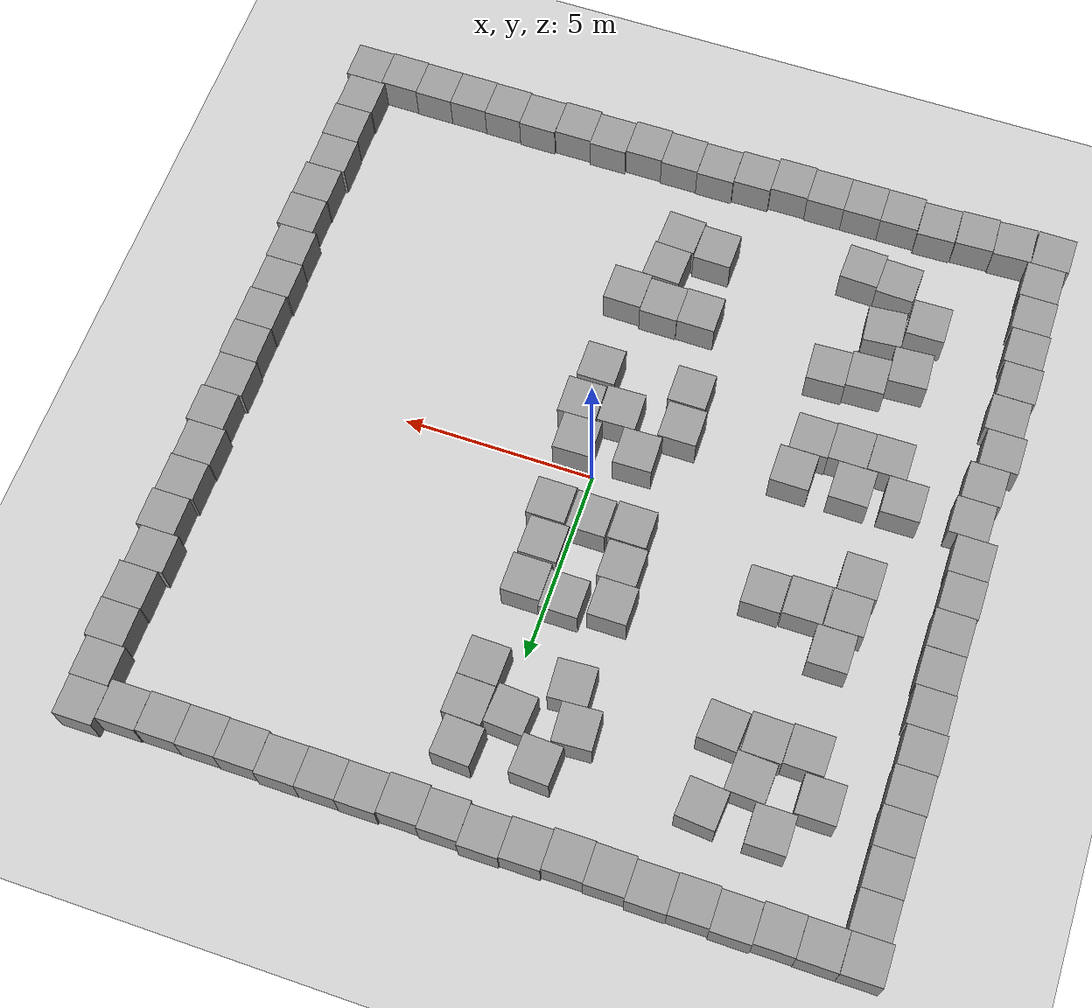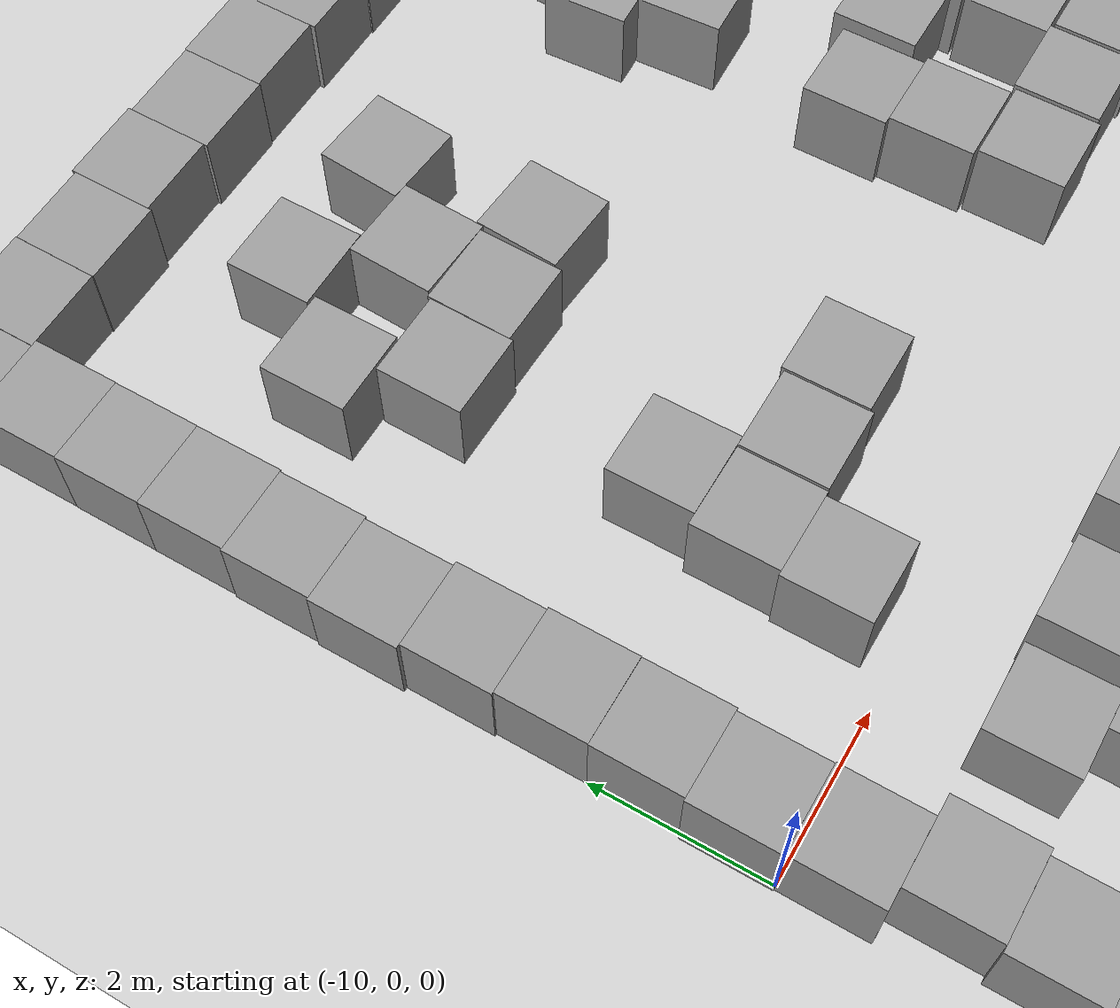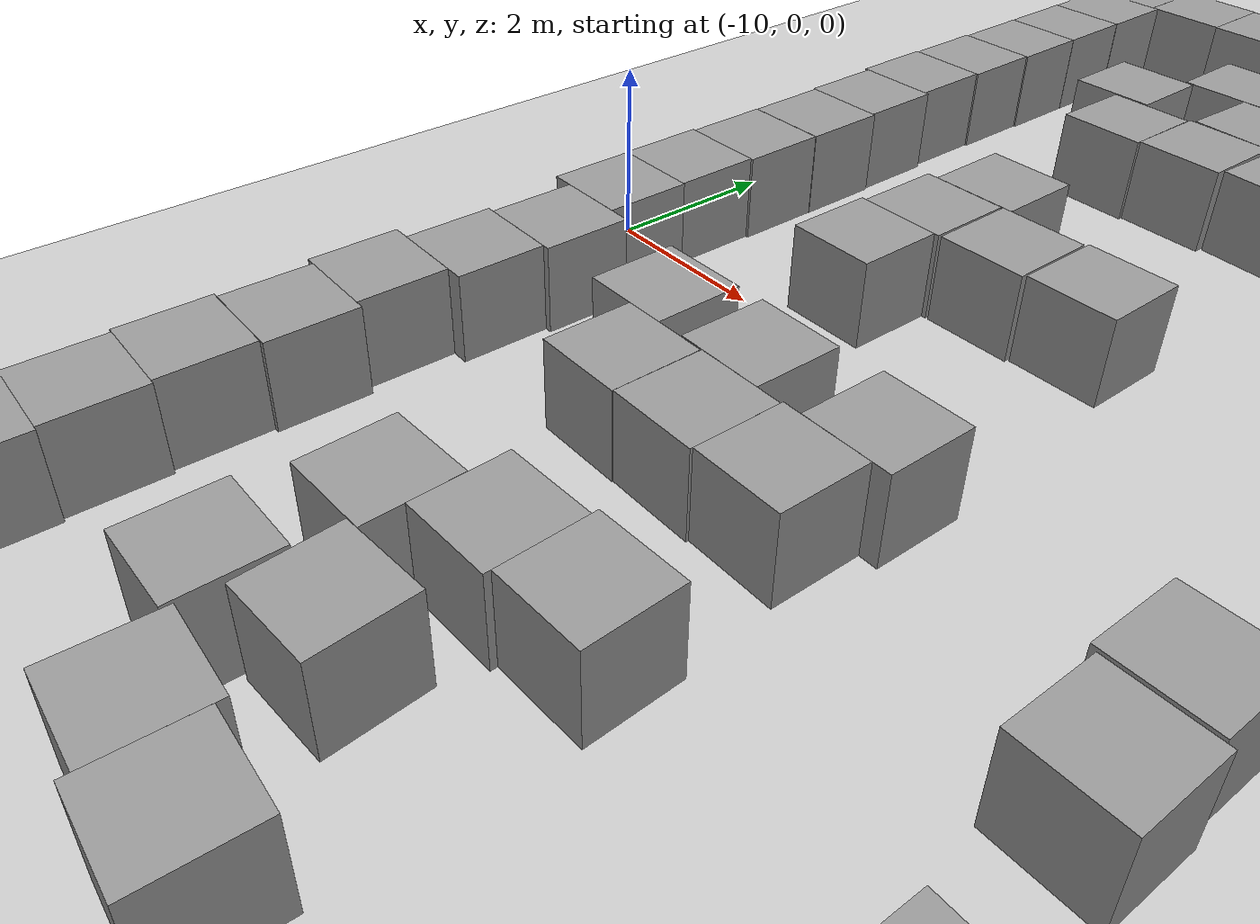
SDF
<sdf version="1.7">
 <world name="default">
  <light name="sun" type="directional">
   <pose>0 0 10 0 -0 0</pose>
   <diffuse>0.8 0.8 0.8 1</diffuse>
   <specular>0.2 0.2 0.2 1</specular>
   <attenuation>
    <range>1000</range>
    <constant>0.9</constant>
    <linear>0.01</linear>
    <quadratic>0.001</quadratic>
   </attenuation>
   <direction>-0.5 0.1 -0.9</direction>
   <spot><inner_angle>0</inner_angle><outer_angle>0</outer_angle><falloff>0</falloff></spot>
  </light>
  <model name="ground_plane">
   <static>1</static>
   <link name="link">
    <collision name="collision">
     <geometry><plane><normal>0 0 1</normal><size>100 100</size></plane></geometry>
     <surface>
      <contact><collide_bitmask>65535</collide_bitmask></contact>
      <friction><ode><mu>100</mu><mu2>50</mu2></ode></friction>
     </surface>
    </collision>
    <visual name="visual">
     <cast_shadows>0</cast_shadows>
     <geometry><plane><normal>0 0 1</normal><size>100 100</size></plane></geometry>
     <material>
      <script><uri>file://media/materials/scripts/gazebo.material</uri><name>Gazebo/Grey</name></script>
     </material>
    </visual>
   </link>
  </model>
  <gravity>0 0 -9.8</gravity>
  <magnetic_field>6e-06 2.3e-05 -4.2e-05</magnetic_field>
  <atmosphere type="adiabatic"/>
  <physics type="ode">
   <max_step_size>0.001</max_step_size>
   <real_time_factor>1</real_time_factor>
   <real_time_update_rate>1000</real_time_update_rate>
  </physics>
  <scene><ambient>0.4 0.4 0.4 1</ambient><background>0.7 0.7 0.7 1</background><shadows>1</shadows></scene>
  <audio><device>default</device></audio>
  <spherical_coordinates>
   <surface_model>EARTH_WGS84</surface_model>
   <latitude_deg>0</latitude_deg>
   <longitude_deg>0</longitude_deg>
   <elevation>0</elevation>
   <heading_deg>0</heading_deg>
  </spherical_coordinates>
  <model name="unit_box">
   <pose>-9.50922 1.49297 0.499995 0 -1e-05 -0.001719</pose>
   <link name="link">
    <inertial>
     <mass>1</mass>
     <inertia>
      <ixx>0.166667</ixx>
      <ixy>0</ixy>
      <ixz>0</ixz>
      <iyy>0.166667</iyy>
      <iyz>0</iyz>
      <izz>0.166667</izz>
     </inertia>
    </inertial>
    <collision name="collision"><geometry><box><size>1 1 1</size></box></geometry></collision>
    <visual name="visual">
     <geometry><box><size>1 1 1</size></box></geometry>
     <material>
      <script><name>Gazebo/Grey</name><uri>file://media/materials/scripts/gazebo.material</uri></script>
     </material>
    </visual>
   </link>
  </model>
  <model name="unit_box_0">
   <pose>-9.50449 2.49462 0.499995 0 -1e-05 0.001596</pose>
   <link name="link">
    <inertial>
     <mass>1</mass>
     <inertia>
      <ixx>0.166667</ixx>
      <ixy>0</ixy>
      <ixz>0</ixz>
      <iyy>0.166667</iyy>
      <iyz>0</iyz>
      <izz>0.166667</izz>
     </inertia>
    </inertial>
    <collision name="collision"><geometry><box><size>1 1 1</size></box></geometry></collision>
    <visual name="visual">
     <geometry><box><size>1 1 1</size></box></geometry>
     <material>
      <script><name>Gazebo/Grey</name><uri>file://media/materials/scripts/gazebo.material</uri></script>
     </material>
    </visual>
   </link>
  </model>
  <model name="unit_box_1">
   <pose>-9.53013 3.49459 0.499995 0 1e-05 0.001611</pose>
   <link name="link">
    <inertial>
     <mass>1</mass>
     <inertia>
      <ixx>0.166667</ixx>
      <ixy>0</ixy>
      <ixz>0</ixz>
      <iyy>0.166667</iyy>
      <iyz>0</iyz>
      <izz>0.166667</izz>
     </inertia>
    </inertial>
    <collision name="collision"><geometry><box><size>1 1 1</size></box></geometry></collision>
    <visual name="visual">
     <geometry><box><size>1 1 1</size></box></geometry>
     <material>
      <script><name>Gazebo/Grey</name><uri>file://media/materials/scripts/gazebo.material</uri></script>
     </material>
    </visual>
   </link>
  </model>
  <model name="unit_box_2">
   <pose>-9.57917 4.49452 0.499995 0 1e-05 0.001623</pose>
   <link name="link">
    <inertial>
     <mass>1</mass>
     <inertia>
      <ixx>0.166667</ixx>
      <ixy>0</ixy>
      <ixz>0</ixz>
      <iyy>0.166667</iyy>
      <iyz>0</iyz>
      <izz>0.166667</izz>
     </inertia>
    </inertial>
    <collision name="collision"><geometry><box><size>1 1 1</size></box></geometry></collision>
    <visual name="visual">
     <geometry><box><size>1 1 1</size></box></geometry>
     <material>
      <script><name>Gazebo/Grey</name><uri>file://media/materials/scripts/gazebo.material</uri></script>
     </material>
    </visual>
   </link>
  </model>
  <model name="unit_box_3">
   <pose>-9.55846 5.49458 0.499995 -1e-05 -0 0.001623</pose>
   <link name="link">
    <inertial>
     <mass>1</mass>
     <inertia>
      <ixx>0.166667</ixx>
      <ixy>0</ixy>
      <ixz>0</ixz>
      <iyy>0.166667</iyy>
      <iyz>0</iyz>
      <izz>0.166667</izz>
     </inertia>
    </inertial>
    <collision name="collision"><geometry><box><size>1 1 1</size></box></geometry></collision>
    <visual name="visual">
     <geometry><box><size>1 1 1</size></box></geometry>
     <material>
      <script><name>Gazebo/Grey</name><uri>file://media/materials/scripts/gazebo.material</uri></script>
     </material>
    </visual>
   </link>
  </model>
  <model name="unit_box_4">
   <pose>-9.54077 6.4946 0.499995 1e-05 0 0.001625</pose>
   <link name="link">
    <inertial>
     <mass>1</mass>
     <inertia>
      <ixx>0.166667</ixx>
      <ixy>0</ixy>
      <ixz>0</ixz>
      <iyy>0.166667</iyy>
      <iyz>0</iyz>
      <izz>0.166667</izz>
     </inertia>
    </inertial>
    <collision name="collision"><geometry><box><size>1 1 1</size></box></geometry></collision>
    <visual name="visual">
     <geometry><box><size>1 1 1</size></box></geometry>
     <material>
      <script><name>Gazebo/Grey</name><uri>file://media/materials/scripts/gazebo.material</uri></script>
     </material>
    </visual>
   </link>
  </model>
  <model name="unit_box_5">
   <pose>-9.54003 7.49461 0.499995 1e-05 0 0.001625</pose>
   <link name="link">
    <inertial>
     <mass>1</mass>
     <inertia>
      <ixx>0.166667</ixx>
      <ixy>0</ixy>
      <ixz>0</ixz>
      <iyy>0.166667</iyy>
      <iyz>0</iyz>
      <izz>0.166667</izz>
     </inertia>
    </inertial>
    <collision name="collision"><geometry><box><size>1 1 1</size></box></geometry></collision>
    <visual name="visual">
     <geometry><box><size>1 1 1</size></box></geometry>
     <material>
      <script><name>Gazebo/Grey</name><uri>file://media/materials/scripts/gazebo.material</uri></script>
     </material>
    </visual>
   </link>
  </model>
  <model name="unit_box_6">
   <pose>-9.53697 8.49462 0.499995 1e-05 0 0.001625</pose>
   <link name="link">
    <inertial>
     <mass>1</mass>
     <inertia>
      <ixx>0.166667</ixx>
      <ixy>0</ixy>
      <ixz>0</ixz>
      <iyy>0.166667</iyy>
      <iyz>0</iyz>
      <izz>0.166667</izz>
     </inertia>
    </inertial>
    <collision name="collision"><geometry><box><size>1 1 1</size></box></geometry></collision>
    <visual name="visual">
     <geometry><box><size>1 1 1</size></box></geometry>
     <material>
      <script><name>Gazebo/Grey</name><uri>file://media/materials/scripts/gazebo.material</uri></script>
     </material>
    </visual>
   </link>
  </model>
  <model name="unit_box_7">
   <pose>-9.61342 9.4945 0.499995 1e-05 0 0.001626</pose>
   <link name="link">
    <inertial>
     <mass>1</mass>
     <inertia>
      <ixx>0.166667</ixx>
      <ixy>0</ixy>
      <ixz>0</ixz>
      <iyy>0.166667</iyy>
      <iyz>0</iyz>
      <izz>0.166667</izz>
     </inertia>
    </inertial>
    <collision name="collision"><geometry><box><size>1 1 1</size></box></geometry></collision>
    <visual name="visual">
     <geometry><box><size>1 1 1</size></box></geometry>
     <material>
      <script><name>Gazebo/Grey</name><uri>file://media/materials/scripts/gazebo.material</uri></script>
     </material>
    </visual>
   </link>
  </model>
  <model name="unit_box_8">
   <pose>-8.61032 9.49388 0.499995 -0 1e-05 -0.003673</pose>
   <link name="link">
    <inertial>
     <mass>1</mass>
     <inertia>
      <ixx>0.166667</ixx>
      <ixy>0</ixy>
      <ixz>0</ixz>
      <iyy>0.166667</iyy>
      <iyz>0</iyz>
      <izz>0.166667</izz>
     </inertia>
    </inertial>
    <collision name="collision"><geometry><box><size>1 1 1</size></box></geometry></collision>
    <visual name="visual">
     <geometry><box><size>1 1 1</size></box></geometry>
     <material>
      <script><name>Gazebo/Grey</name><uri>file://media/materials/scripts/gazebo.material</uri></script>
     </material>
    </visual>
   </link>
  </model>
  <model name="unit_box_9">
   <pose>-7.61018 9.47879 0.499995 0 1e-05 -0.003293</pose>
   <link name="link">
    <inertial>
     <mass>1</mass>
     <inertia>
      <ixx>0.166667</ixx>
      <ixy>0</ixy>
      <ixz>0</ixz>
      <iyy>0.166667</iyy>
      <iyz>0</iyz>
      <izz>0.166667</izz>
     </inertia>
    </inertial>
    <collision name="collision"><geometry><box><size>1 1 1</size></box></geometry></collision>
    <visual name="visual">
     <geometry><box><size>1 1 1</size></box></geometry>
     <material>
      <script><name>Gazebo/Grey</name><uri>file://media/materials/scripts/gazebo.material</uri></script>
     </material>
    </visual>
   </link>
  </model>
  <model name="unit_box_10">
   <pose>-6.60926 9.52215 0.499995 1e-05 -0 -0.001603</pose>
   <link name="link">
    <inertial>
     <mass>1</mass>
     <inertia>
      <ixx>0.166667</ixx>
      <ixy>0</ixy>
      <ixz>0</ixz>
      <iyy>0.166667</iyy>
      <iyz>0</iyz>
      <izz>0.166667</izz>
     </inertia>
    </inertial>
    <collision name="collision"><geometry><box><size>1 1 1</size></box></geometry></collision>
    <visual name="visual">
     <geometry><box><size>1 1 1</size></box></geometry>
     <material>
      <script><name>Gazebo/Grey</name><uri>file://media/materials/scripts/gazebo.material</uri></script>
     </material>
    </visual>
   </link>
  </model>
  <model name="unit_box_11">
   <pose>-5.60932 9.47912 0.499995 1e-05 -0 -0.001602</pose>
   <link name="link">
    <inertial>
     <mass>1</mass>
     <inertia>
      <ixx>0.166667</ixx>
      <ixy>0</ixy>
      <ixz>0</ixz>
      <iyy>0.166667</iyy>
      <iyz>0</iyz>
      <izz>0.166667</izz>
     </inertia>
    </inertial>
    <collision name="collision"><geometry><box><size>1 1 1</size></box></geometry></collision>
    <visual name="visual">
     <geometry><box><size>1 1 1</size></box></geometry>
     <material>
      <script><name>Gazebo/Grey</name><uri>file://media/materials/scripts/gazebo.material</uri></script>
     </material>
    </visual>
   </link>
  </model>
  <model name="unit_box_12">
   <pose>-4.60924 9.49284 0.499995 -1e-05 -0 -0.001499</pose>
   <link name="link">
    <inertial>
     <mass>1</mass>
     <inertia>
      <ixx>0.166667</ixx>
      <ixy>0</ixy>
      <ixz>0</ixz>
      <iyy>0.166667</iyy>
      <iyz>0</iyz>
      <izz>0.166667</izz>
     </inertia>
    </inertial>
    <collision name="collision"><geometry><box><size>1 1 1</size></box></geometry></collision>
    <visual name="visual">
     <geometry><box><size>1 1 1</size></box></geometry>
     <material>
      <script><name>Gazebo/Grey</name><uri>file://media/materials/scripts/gazebo.material</uri></script>
     </material>
    </visual>
   </link>
  </model>
  <model name="unit_box_13">
   <pose>-3.60932 9.43189 0.499995 1e-05 0 -0.001485</pose>
   <link name="link">
    <inertial>
     <mass>1</mass>
     <inertia>
      <ixx>0.166667</ixx>
      <ixy>0</ixy>
      <ixz>0</ixz>
      <iyy>0.166667</iyy>
      <iyz>0</iyz>
      <izz>0.166667</izz>
     </inertia>
    </inertial>
    <collision name="collision"><geometry><box><size>1 1 1</size></box></geometry></collision>
    <visual name="visual">
     <geometry><box><size>1 1 1</size></box></geometry>
     <material>
      <script><name>Gazebo/Grey</name><uri>file://media/materials/scripts/gazebo.material</uri></script>
     </material>
    </visual>
   </link>
  </model>
  <model name="unit_box_14">
   <pose>-2.60928 9.41153 0.499995 0 -9e-06 -0.001348</pose>
   <link name="link">
    <inertial>
     <mass>1</mass>
     <inertia>
      <ixx>0.166667</ixx>
      <ixy>0</ixy>
      <ixz>0</ixz>
      <iyy>0.166667</iyy>
      <iyz>0</iyz>
      <izz>0.166667</izz>
     </inertia>
    </inertial>
    <collision name="collision"><geometry><box><size>1 1 1</size></box></geometry></collision>
    <visual name="visual">
     <geometry><box><size>1 1 1</size></box></geometry>
     <material>
      <script><name>Gazebo/Grey</name><uri>file://media/materials/scripts/gazebo.material</uri></script>
     </material>
    </visual>
   </link>
  </model>
  <model name="unit_box_15">
   <pose>-1.60915 9.46987 0.499995 -0 9e-06 -0.001269</pose>
   <link name="link">
    <inertial>
     <mass>1</mass>
     <inertia>
      <ixx>0.166667</ixx>
      <ixy>0</ixy>
      <ixz>0</ixz>
      <iyy>0.166667</iyy>
      <iyz>0</iyz>
      <izz>0.166667</izz>
     </inertia>
    </inertial>
    <collision name="collision"><geometry><box><size>1 1 1</size></box></geometry></collision>
    <visual name="visual">
     <geometry><box><size>1 1 1</size></box></geometry>
     <material>
      <script><name>Gazebo/Grey</name><uri>file://media/materials/scripts/gazebo.material</uri></script>
     </material>
    </visual>
   </link>
  </model>
  <model name="unit_box_16">
   <pose>-0.609072 9.50819 0.499995 -0 1e-05 -0.001209</pose>
   <link name="link">
    <inertial>
     <mass>1</mass>
     <inertia>
      <ixx>0.166667</ixx>
      <ixy>0</ixy>
      <ixz>0</ixz>
      <iyy>0.166667</iyy>
      <iyz>0</iyz>
      <izz>0.166667</izz>
     </inertia>
    </inertial>
    <collision name="collision"><geometry><box><size>1 1 1</size></box></geometry></collision>
    <visual name="visual">
     <geometry><box><size>1 1 1</size></box></geometry>
     <material>
      <script><name>Gazebo/Grey</name><uri>file://media/materials/scripts/gazebo.material</uri></script>
     </material>
    </visual>
   </link>
  </model>
  <model name="unit_box_17">
   <pose>0.390916 9.43627 0.499995 1e-05 0 -0.001064</pose>
   <link name="link">
    <inertial>
     <mass>1</mass>
     <inertia>
      <ixx>0.166667</ixx>
      <ixy>0</ixy>
      <ixz>0</ixz>
      <iyy>0.166667</iyy>
      <iyz>0</iyz>
      <izz>0.166667</izz>
     </inertia>
    </inertial>
    <collision name="collision"><geometry><box><size>1 1 1</size></box></geometry></collision>
    <visual name="visual">
     <geometry><box><size>1 1 1</size></box></geometry>
     <material>
      <script><name>Gazebo/Grey</name><uri>file://media/materials/scripts/gazebo.material</uri></script>
     </material>
    </visual>
   </link>
  </model>
  <model name="unit_box_18">
   <pose>1.39091 9.39225 0.499995 0 -1e-05 -0.001016</pose>
   <link name="link">
    <inertial>
     <mass>1</mass>
     <inertia>
      <ixx>0.166667</ixx>
      <ixy>0</ixy>
      <ixz>0</ixz>
      <iyy>0.166667</iyy>
      <iyz>0</iyz>
      <izz>0.166667</izz>
     </inertia>
    </inertial>
    <collision name="collision"><geometry><box><size>1 1 1</size></box></geometry></collision>
    <visual name="visual">
     <geometry><box><size>1 1 1</size></box></geometry>
     <material>
      <script><name>Gazebo/Grey</name><uri>file://media/materials/scripts/gazebo.material</uri></script>
     </material>
    </visual>
   </link>
  </model>
  <model name="unit_box_19">
   <pose>2.39096 9.4387 0.499995 0 -1e-05 -0.001018</pose>
   <link name="link">
    <inertial>
     <mass>1</mass>
     <inertia>
      <ixx>0.166667</ixx>
      <ixy>0</ixy>
      <ixz>0</ixz>
      <iyy>0.166667</iyy>
      <iyz>0</iyz>
      <izz>0.166667</izz>
     </inertia>
    </inertial>
    <collision name="collision"><geometry><box><size>1 1 1</size></box></geometry></collision>
    <visual name="visual">
     <geometry><box><size>1 1 1</size></box></geometry>
     <material>
      <script><name>Gazebo/Grey</name><uri>file://media/materials/scripts/gazebo.material</uri></script>
     </material>
    </visual>
   </link>
  </model>
  <model name="unit_box_20">
   <pose>3.39095 9.42951 0.499995 0 -1e-05 -0.001017</pose>
   <link name="link">
    <inertial>
     <mass>1</mass>
     <inertia>
      <ixx>0.166667</ixx>
      <ixy>0</ixy>
      <ixz>0</ixz>
      <iyy>0.166667</iyy>
      <iyz>0</iyz>
      <izz>0.166667</izz>
     </inertia>
    </inertial>
    <collision name="collision"><geometry><box><size>1 1 1</size></box></geometry></collision>
    <visual name="visual">
     <geometry><box><size>1 1 1</size></box></geometry>
     <material>
      <script><name>Gazebo/Grey</name><uri>file://media/materials/scripts/gazebo.material</uri></script>
     </material>
    </visual>
   </link>
  </model>
  <model name="unit_box_21">
   <pose>4.39095 9.43121 0.499995 0 -1e-05 -0.001014</pose>
   <link name="link">
    <inertial>
     <mass>1</mass>
     <inertia>
      <ixx>0.166667</ixx>
      <ixy>0</ixy>
      <ixz>0</ixz>
      <iyy>0.166667</iyy>
      <iyz>0</iyz>
      <izz>0.166667</izz>
     </inertia>
    </inertial>
    <collision name="collision"><geometry><box><size>1 1 1</size></box></geometry></collision>
    <visual name="visual">
     <geometry><box><size>1 1 1</size></box></geometry>
     <material>
      <script><name>Gazebo/Grey</name><uri>file://media/materials/scripts/gazebo.material</uri></script>
     </material>
    </visual>
   </link>
  </model>
  <model name="unit_box_22">
   <pose>5.39168 9.38598 0.5 -0 1e-06 0.000489</pose>
   <link name="link">
    <inertial>
     <mass>1</mass>
     <inertia>
      <ixx>0.166667</ixx>
      <ixy>0</ixy>
      <ixz>0</ixz>
      <iyy>0.166667</iyy>
      <iyz>0</iyz>
      <izz>0.166667</izz>
     </inertia>
    </inertial>
    <collision name="collision"><geometry><box><size>1 1 1</size></box></geometry></collision>
    <visual name="visual">
     <geometry><box><size>1 1 1</size></box></geometry>
     <material>
      <script><name>Gazebo/Grey</name><uri>file://media/materials/scripts/gazebo.material</uri></script>
     </material>
    </visual>
   </link>
  </model>
  <model name="unit_box_23">
   <pose>6.39168 9.37903 0.5 0 -1e-06 0.000489</pose>
   <link name="link">
    <inertial>
     <mass>1</mass>
     <inertia>
      <ixx>0.166667</ixx>
      <ixy>0</ixy>
      <ixz>0</ixz>
      <iyy>0.166667</iyy>
      <iyz>0</iyz>
      <izz>0.166667</izz>
     </inertia>
    </inertial>
    <collision name="collision"><geometry><box><size>1 1 1</size></box></geometry></collision>
    <visual name="visual">
     <geometry><box><size>1 1 1</size></box></geometry>
     <material>
      <script><name>Gazebo/Grey</name><uri>file://media/materials/scripts/gazebo.material</uri></script>
     </material>
    </visual>
   </link>
  </model>
  <model name="unit_box_24">
   <pose>7.39182 9.36826 0.499995 -1e-05 0 0.00073</pose>
   <link name="link">
    <inertial>
     <mass>1</mass>
     <inertia>
      <ixx>0.166667</ixx>
      <ixy>0</ixy>
      <ixz>0</ixz>
      <iyy>0.166667</iyy>
      <iyz>0</iyz>
      <izz>0.166667</izz>
     </inertia>
    </inertial>
    <collision name="collision"><geometry><box><size>1 1 1</size></box></geometry></collision>
    <visual name="visual">
     <geometry><box><size>1 1 1</size></box></geometry>
     <material>
      <script><name>Gazebo/Grey</name><uri>file://media/materials/scripts/gazebo.material</uri></script>
     </material>
    </visual>
   </link>
  </model>
  <model name="unit_box_25">
   <pose>8.39215 9.39462 0.499995 1e-05 -0 0.001466</pose>
   <link name="link">
    <inertial>
     <mass>1</mass>
     <inertia>
      <ixx>0.166667</ixx>
      <ixy>0</ixy>
      <ixz>0</ixz>
      <iyy>0.166667</iyy>
      <iyz>0</iyz>
      <izz>0.166667</izz>
     </inertia>
    </inertial>
    <collision name="collision"><geometry><box><size>1 1 1</size></box></geometry></collision>
    <visual name="visual">
     <geometry><box><size>1 1 1</size></box></geometry>
     <material>
      <script><name>Gazebo/Grey</name><uri>file://media/materials/scripts/gazebo.material</uri></script>
     </material>
    </visual>
   </link>
  </model>
  <model name="unit_box_26">
   <pose>9.39272 9.59432 0.499995 0 1e-05 0.000277</pose>
   <link name="link">
    <inertial>
     <mass>1</mass>
     <inertia>
      <ixx>0.166667</ixx>
      <ixy>0</ixy>
      <ixz>0</ixz>
      <iyy>0.166667</iyy>
      <iyz>0</iyz>
      <izz>0.166667</izz>
     </inertia>
    </inertial>
    <collision name="collision"><geometry><box><size>1 1 1</size></box></geometry></collision>
    <visual name="visual">
     <geometry><box><size>1 1 1</size></box></geometry>
     <material>
      <script><name>Gazebo/Grey</name><uri>file://media/materials/scripts/gazebo.material</uri></script>
     </material>
    </visual>
   </link>
  </model>
  <model name="unit_box_27">
   <pose>9.41845 8.59432 0.499995 0 1e-05 0.000287</pose>
   <link name="link">
    <inertial>
     <mass>1</mass>
     <inertia>
      <ixx>0.166667</ixx>
      <ixy>0</ixy>
      <ixz>0</ixz>
      <iyy>0.166667</iyy>
      <iyz>0</iyz>
      <izz>0.166667</izz>
     </inertia>
    </inertial>
    <collision name="collision"><geometry><box><size>1 1 1</size></box></geometry></collision>
    <visual name="visual">
     <geometry><box><size>1 1 1</size></box></geometry>
     <material>
      <script><name>Gazebo/Grey</name><uri>file://media/materials/scripts/gazebo.material</uri></script>
     </material>
    </visual>
   </link>
  </model>
  <model name="unit_box_28">
   <pose>9.49662 7.59431 0.499995 1e-05 -0 0.000314</pose>
   <link name="link">
    <inertial>
     <mass>1</mass>
     <inertia>
      <ixx>0.166667</ixx>
      <ixy>0</ixy>
      <ixz>0</ixz>
      <iyy>0.166667</iyy>
      <iyz>0</iyz>
      <izz>0.166667</izz>
     </inertia>
    </inertial>
    <collision name="collision"><geometry><box><size>1 1 1</size></box></geometry></collision>
    <visual name="visual">
     <geometry><box><size>1 1 1</size></box></geometry>
     <material>
      <script><name>Gazebo/Grey</name><uri>file://media/materials/scripts/gazebo.material</uri></script>
     </material>
    </visual>
   </link>
  </model>
  <model name="unit_box_29">
   <pose>9.47482 6.59424 0.499995 1e-05 0 0.000426</pose>
   <link name="link">
    <inertial>
     <mass>1</mass>
     <inertia>
      <ixx>0.166667</ixx>
      <ixy>0</ixy>
      <ixz>0</ixz>
      <iyy>0.166667</iyy>
      <iyz>0</iyz>
      <izz>0.166667</izz>
     </inertia>
    </inertial>
    <collision name="collision"><geometry><box><size>1 1 1</size></box></geometry></collision>
    <visual name="visual">
     <geometry><box><size>1 1 1</size></box></geometry>
     <material>
      <script><name>Gazebo/Grey</name><uri>file://media/materials/scripts/gazebo.material</uri></script>
     </material>
    </visual>
   </link>
  </model>
  <model name="unit_box_30">
   <pose>9.3664 5.59394 0.5 0 -0 0.000939</pose>
   <link name="link">
    <inertial>
     <mass>1</mass>
     <inertia>
      <ixx>0.166667</ixx>
      <ixy>0</ixy>
      <ixz>0</ixz>
      <iyy>0.166667</iyy>
      <iyz>0</iyz>
      <izz>0.166667</izz>
     </inertia>
    </inertial>
    <collision name="collision"><geometry><box><size>1 1 1</size></box></geometry></collision>
    <visual name="visual">
     <geometry><box><size>1 1 1</size></box></geometry>
     <material>
      <script><name>Gazebo/Grey</name><uri>file://media/materials/scripts/gazebo.material</uri></script>
     </material>
    </visual>
   </link>
  </model>
  <model name="unit_box_31">
   <pose>9.50764 4.59388 0.499995 1e-05 -0 0.001457</pose>
   <link name="link">
    <inertial>
     <mass>1</mass>
     <inertia>
      <ixx>0.166667</ixx>
      <ixy>0</ixy>
      <ixz>0</ixz>
      <iyy>0.166667</iyy>
      <iyz>0</iyz>
      <izz>0.166667</izz>
     </inertia>
    </inertial>
    <collision name="collision"><geometry><box><size>1 1 1</size></box></geometry></collision>
    <visual name="visual">
     <geometry><box><size>1 1 1</size></box></geometry>
     <material>
      <script><name>Gazebo/Grey</name><uri>file://media/materials/scripts/gazebo.material</uri></script>
     </material>
    </visual>
   </link>
  </model>
  <model name="unit_box_32">
   <pose>9.44962 3.59379 0.499995 1e-05 0 0.001464</pose>
   <link name="link">
    <inertial>
     <mass>1</mass>
     <inertia>
      <ixx>0.166667</ixx>
      <ixy>0</ixy>
      <ixz>0</ixz>
      <iyy>0.166667</iyy>
      <iyz>0</iyz>
      <izz>0.166667</izz>
     </inertia>
    </inertial>
    <collision name="collision"><geometry><box><size>1 1 1</size></box></geometry></collision>
    <visual name="visual">
     <geometry><box><size>1 1 1</size></box></geometry>
     <material>
      <script><name>Gazebo/Grey</name><uri>file://media/materials/scripts/gazebo.material</uri></script>
     </material>
    </visual>
   </link>
  </model>
  <model name="unit_box_33">
   <pose>9.41917 2.59372 0.499995 1e-05 -0 0.001487</pose>
   <link name="link">
    <inertial>
     <mass>1</mass>
     <inertia>
      <ixx>0.166667</ixx>
      <ixy>0</ixy>
      <ixz>0</ixz>
      <iyy>0.166667</iyy>
      <iyz>0</iyz>
      <izz>0.166667</izz>
     </inertia>
    </inertial>
    <collision name="collision"><geometry><box><size>1 1 1</size></box></geometry></collision>
    <visual name="visual">
     <geometry><box><size>1 1 1</size></box></geometry>
     <material>
      <script><name>Gazebo/Grey</name><uri>file://media/materials/scripts/gazebo.material</uri></script>
     </material>
    </visual>
   </link>
  </model>
  <model name="unit_box_34">
   <pose>9.50067 1.59382 0.499995 -1e-05 -0 0.001551</pose>
   <link name="link">
    <inertial>
     <mass>1</mass>
     <inertia>
      <ixx>0.166667</ixx>
      <ixy>0</ixy>
      <ixz>0</ixz>
      <iyy>0.166667</iyy>
      <iyz>0</iyz>
      <izz>0.166667</izz>
     </inertia>
    </inertial>
    <collision name="collision"><geometry><box><size>1 1 1</size></box></geometry></collision>
    <visual name="visual">
     <geometry><box><size>1 1 1</size></box></geometry>
     <material>
      <script><name>Gazebo/Grey</name><uri>file://media/materials/scripts/gazebo.material</uri></script>
     </material>
    </visual>
   </link>
  </model>
  <model name="unit_box_35">
   <pose>9.42389 0.593646 0.499995 1e-05 -0 0.001635</pose>
   <link name="link">
    <inertial>
     <mass>1</mass>
     <inertia>
      <ixx>0.166667</ixx>
      <ixy>0</ixy>
      <ixz>0</ixz>
      <iyy>0.166667</iyy>
      <iyz>0</iyz>
      <izz>0.166667</izz>
     </inertia>
    </inertial>
    <collision name="collision"><geometry><box><size>1 1 1</size></box></geometry></collision>
    <visual name="visual">
     <geometry><box><size>1 1 1</size></box></geometry>
     <material>
      <script><name>Gazebo/Grey</name><uri>file://media/materials/scripts/gazebo.material</uri></script>
     </material>
    </visual>
   </link>
  </model>
  <model name="unit_box_36">
   <pose>9.45115 -0.406326 0.499995 0 -1e-05 0.001611</pose>
   <link name="link">
    <inertial>
     <mass>1</mass>
     <inertia>
      <ixx>0.166667</ixx>
      <ixy>0</ixy>
      <ixz>0</ixz>
      <iyy>0.166667</iyy>
      <iyz>0</iyz>
      <izz>0.166667</izz>
     </inertia>
    </inertial>
    <collision name="collision"><geometry><box><size>1 1 1</size></box></geometry></collision>
    <visual name="visual">
     <geometry><box><size>1 1 1</size></box></geometry>
     <material>
      <script><name>Gazebo/Grey</name><uri>file://media/materials/scripts/gazebo.material</uri></script>
     </material>
    </visual>
   </link>
  </model>
  <model name="unit_box_37">
   <pose>9.43994 -1.40635 0.499995 -0 -1e-05 0.00161</pose>
   <link name="link">
    <inertial>
     <mass>1</mass>
     <inertia>
      <ixx>0.166667</ixx>
      <ixy>0</ixy>
      <ixz>0</ixz>
      <iyy>0.166667</iyy>
      <iyz>0</iyz>
      <izz>0.166667</izz>
     </inertia>
    </inertial>
    <collision name="collision"><geometry><box><size>1 1 1</size></box></geometry></collision>
    <visual name="visual">
     <geometry><box><size>1 1 1</size></box></geometry>
     <material>
      <script><name>Gazebo/Grey</name><uri>file://media/materials/scripts/gazebo.material</uri></script>
     </material>
    </visual>
   </link>
  </model>
  <model name="unit_box_38">
   <pose>9.40093 -2.40644 0.499995 0 -1e-05 0.001587</pose>
   <link name="link">
    <inertial>
     <mass>1</mass>
     <inertia>
      <ixx>0.166667</ixx>
      <ixy>0</ixy>
      <ixz>0</ixz>
      <iyy>0.166667</iyy>
      <iyz>0</iyz>
      <izz>0.166667</izz>
     </inertia>
    </inertial>
    <collision name="collision"><geometry><box><size>1 1 1</size></box></geometry></collision>
    <visual name="visual">
     <geometry><box><size>1 1 1</size></box></geometry>
     <material>
      <script><name>Gazebo/Grey</name><uri>file://media/materials/scripts/gazebo.material</uri></script>
     </material>
    </visual>
   </link>
  </model>
  <model name="unit_box_39">
   <pose>9.42291 -3.40644 0.499995 1e-05 -0 0.001552</pose>
   <link name="link">
    <inertial>
     <mass>1</mass>
     <inertia>
      <ixx>0.166667</ixx>
      <ixy>0</ixy>
      <ixz>0</ixz>
      <iyy>0.166667</iyy>
      <iyz>0</iyz>
      <izz>0.166667</izz>
     </inertia>
    </inertial>
    <collision name="collision"><geometry><box><size>1 1 1</size></box></geometry></collision>
    <visual name="visual">
     <geometry><box><size>1 1 1</size></box></geometry>
     <material>
      <script><name>Gazebo/Grey</name><uri>file://media/materials/scripts/gazebo.material</uri></script>
     </material>
    </visual>
   </link>
  </model>
  <model name="unit_box_40">
   <pose>9.53442 -4.40627 0.499995 1e-05 -0 0.001546</pose>
   <link name="link">
    <inertial>
     <mass>1</mass>
     <inertia>
      <ixx>0.166667</ixx>
      <ixy>0</ixy>
      <ixz>0</ixz>
      <iyy>0.166667</iyy>
      <iyz>0</iyz>
      <izz>0.166667</izz>
     </inertia>
    </inertial>
    <collision name="collision"><geometry><box><size>1 1 1</size></box></geometry></collision>
    <visual name="visual">
     <geometry><box><size>1 1 1</size></box></geometry>
     <material>
      <script><name>Gazebo/Grey</name><uri>file://media/materials/scripts/gazebo.material</uri></script>
     </material>
    </visual>
   </link>
  </model>
  <model name="unit_box_41">
   <pose>9.51363 -5.4063 0.499995 -1e-05 -0 0.001535</pose>
   <link name="link">
    <inertial>
     <mass>1</mass>
     <inertia>
      <ixx>0.166667</ixx>
      <ixy>0</ixy>
      <ixz>0</ixz>
      <iyy>0.166667</iyy>
      <iyz>0</iyz>
      <izz>0.166667</izz>
     </inertia>
    </inertial>
    <collision name="collision"><geometry><box><size>1 1 1</size></box></geometry></collision>
    <visual name="visual">
     <geometry><box><size>1 1 1</size></box></geometry>
     <material>
      <script><name>Gazebo/Grey</name><uri>file://media/materials/scripts/gazebo.material</uri></script>
     </material>
    </visual>
   </link>
  </model>
  <model name="unit_box_42">
   <pose>9.4441 -6.40642 0.499995 -1e-05 -0 0.001532</pose>
   <link name="link">
    <inertial>
     <mass>1</mass>
     <inertia>
      <ixx>0.166667</ixx>
      <ixy>0</ixy>
      <ixz>0</ixz>
      <iyy>0.166667</iyy>
      <iyz>0</iyz>
      <izz>0.166667</izz>
     </inertia>
    </inertial>
    <collision name="collision"><geometry><box><size>1 1 1</size></box></geometry></collision>
    <visual name="visual">
     <geometry><box><size>1 1 1</size></box></geometry>
     <material>
      <script><name>Gazebo/Grey</name><uri>file://media/materials/scripts/gazebo.material</uri></script>
     </material>
    </visual>
   </link>
  </model>
  <model name="unit_box_43">
   <pose>9.46387 -7.40639 0.499995 -1e-05 -0 0.001532</pose>
   <link name="link">
    <inertial>
     <mass>1</mass>
     <inertia>
      <ixx>0.166667</ixx>
      <ixy>0</ixy>
      <ixz>0</ixz>
      <iyy>0.166667</iyy>
      <iyz>0</iyz>
      <izz>0.166667</izz>
     </inertia>
    </inertial>
    <collision name="collision"><geometry><box><size>1 1 1</size></box></geometry></collision>
    <visual name="visual">
     <geometry><box><size>1 1 1</size></box></geometry>
     <material>
      <script><name>Gazebo/Grey</name><uri>file://media/materials/scripts/gazebo.material</uri></script>
     </material>
    </visual>
   </link>
  </model>
  <model name="unit_box_44">
   <pose>9.43884 -8.40646 0.499995 -0 1e-05 0.001493</pose>
   <link name="link">
    <inertial>
     <mass>1</mass>
     <inertia>
      <ixx>0.166667</ixx>
      <ixy>0</ixy>
      <ixz>0</ixz>
      <iyy>0.166667</iyy>
      <iyz>0</iyz>
      <izz>0.166667</izz>
     </inertia>
    </inertial>
    <collision name="collision"><geometry><box><size>1 1 1</size></box></geometry></collision>
    <visual name="visual">
     <geometry><box><size>1 1 1</size></box></geometry>
     <material>
      <script><name>Gazebo/Grey</name><uri>file://media/materials/scripts/gazebo.material</uri></script>
     </material>
    </visual>
   </link>
  </model>
  <model name="unit_box_45">
   <pose>9.54897 -9.40792 0.5 0 0 -0.00098</pose>
   <link name="link">
    <inertial>
     <mass>1</mass>
     <inertia>
      <ixx>0.166667</ixx>
      <ixy>0</ixy>
      <ixz>0</ixz>
      <iyy>0.166667</iyy>
      <iyz>0</iyz>
      <izz>0.166667</izz>
     </inertia>
    </inertial>
    <collision name="collision"><geometry><box><size>1 1 1</size></box></geometry></collision>
    <visual name="visual">
     <geometry><box><size>1 1 1</size></box></geometry>
     <material>
      <script><name>Gazebo/Grey</name><uri>file://media/materials/scripts/gazebo.material</uri></script>
     </material>
    </visual>
   </link>
  </model>
  <model name="unit_box_46">
   <pose>8.54892 -9.43223 0.5 -0 -0 -0.000931</pose>
   <link name="link">
    <inertial>
     <mass>1</mass>
     <inertia>
      <ixx>0.166667</ixx>
      <ixy>0</ixy>
      <ixz>0</ixz>
      <iyy>0.166667</iyy>
      <iyz>0</iyz>
      <izz>0.166667</izz>
     </inertia>
    </inertial>
    <collision name="collision"><geometry><box><size>1 1 1</size></box></geometry></collision>
    <visual name="visual">
     <geometry><box><size>1 1 1</size></box></geometry>
     <material>
      <script><name>Gazebo/Grey</name><uri>file://media/materials/scripts/gazebo.material</uri></script>
     </material>
    </visual>
   </link>
  </model>
  <model name="unit_box_47">
   <pose>7.54892 -9.41409 0.499995 -1e-05 -0 -0.000922</pose>
   <link name="link">
    <inertial>
     <mass>1</mass>
     <inertia>
      <ixx>0.166667</ixx>
      <ixy>0</ixy>
      <ixz>0</ixz>
      <iyy>0.166667</iyy>
      <iyz>0</iyz>
      <izz>0.166667</izz>
     </inertia>
    </inertial>
    <collision name="collision"><geometry><box><size>1 1 1</size></box></geometry></collision>
    <visual name="visual">
     <geometry><box><size>1 1 1</size></box></geometry>
     <material>
      <script><name>Gazebo/Grey</name><uri>file://media/materials/scripts/gazebo.material</uri></script>
     </material>
    </visual>
   </link>
  </model>
  <model name="unit_box_48">
   <pose>6.5489 -9.41345 0.499995 0 -1e-05 -0.000895</pose>
   <link name="link">
    <inertial>
     <mass>1</mass>
     <inertia>
      <ixx>0.166667</ixx>
      <ixy>0</ixy>
      <ixz>0</ixz>
      <iyy>0.166667</iyy>
      <iyz>0</iyz>
      <izz>0.166667</izz>
     </inertia>
    </inertial>
    <collision name="collision"><geometry><box><size>1 1 1</size></box></geometry></collision>
    <visual name="visual">
     <geometry><box><size>1 1 1</size></box></geometry>
     <material>
      <script><name>Gazebo/Grey</name><uri>file://media/materials/scripts/gazebo.material</uri></script>
     </material>
    </visual>
   </link>
  </model>
  <model name="unit_box_49">
   <pose>5.54886 -9.40002 0.499995 0 9e-06 -0.000794</pose>
   <link name="link">
    <inertial>
     <mass>1</mass>
     <inertia>
      <ixx>0.166667</ixx>
      <ixy>0</ixy>
      <ixz>0</ixz>
      <iyy>0.166667</iyy>
      <iyz>0</iyz>
      <izz>0.166667</izz>
     </inertia>
    </inertial>
    <collision name="collision"><geometry><box><size>1 1 1</size></box></geometry></collision>
    <visual name="visual">
     <geometry><box><size>1 1 1</size></box></geometry>
     <material>
      <script><name>Gazebo/Grey</name><uri>file://media/materials/scripts/gazebo.material</uri></script>
     </material>
    </visual>
   </link>
  </model>
  <model name="unit_box_50">
   <pose>4.54888 -9.36813 0.499995 0 -1e-05 -0.00079</pose>
   <link name="link">
    <inertial>
     <mass>1</mass>
     <inertia>
      <ixx>0.166667</ixx>
      <ixy>0</ixy>
      <ixz>0</ixz>
      <iyy>0.166667</iyy>
      <iyz>0</iyz>
      <izz>0.166667</izz>
     </inertia>
    </inertial>
    <collision name="collision"><geometry><box><size>1 1 1</size></box></geometry></collision>
    <visual name="visual">
     <geometry><box><size>1 1 1</size></box></geometry>
     <material>
      <script><name>Gazebo/Grey</name><uri>file://media/materials/scripts/gazebo.material</uri></script>
     </material>
    </visual>
   </link>
  </model>
  <model name="unit_box_51">
   <pose>3.54793 -9.42122 0.499995 0 -1e-05 0.00123</pose>
   <link name="link">
    <inertial>
     <mass>1</mass>
     <inertia>
      <ixx>0.166667</ixx>
      <ixy>0</ixy>
      <ixz>0</ixz>
      <iyy>0.166667</iyy>
      <iyz>0</iyz>
      <izz>0.166667</izz>
     </inertia>
    </inertial>
    <collision name="collision"><geometry><box><size>1 1 1</size></box></geometry></collision>
    <visual name="visual">
     <geometry><box><size>1 1 1</size></box></geometry>
     <material>
      <script><name>Gazebo/Grey</name><uri>file://media/materials/scripts/gazebo.material</uri></script>
     </material>
    </visual>
   </link>
  </model>
  <model name="unit_box_52">
   <pose>2.54786 -9.36172 0.499995 0 1e-05 0.001237</pose>
   <link name="link">
    <inertial>
     <mass>1</mass>
     <inertia>
      <ixx>0.166667</ixx>
      <ixy>0</ixy>
      <ixz>0</ixz>
      <iyy>0.166667</iyy>
      <iyz>0</iyz>
      <izz>0.166667</izz>
     </inertia>
    </inertial>
    <collision name="collision"><geometry><box><size>1 1 1</size></box></geometry></collision>
    <visual name="visual">
     <geometry><box><size>1 1 1</size></box></geometry>
     <material>
      <script><name>Gazebo/Grey</name><uri>file://media/materials/scripts/gazebo.material</uri></script>
     </material>
    </visual>
   </link>
  </model>
  <model name="unit_box_53">
   <pose>1.54794 -9.43498 0.499995 1e-05 -0 0.001245</pose>
   <link name="link">
    <inertial>
     <mass>1</mass>
     <inertia>
      <ixx>0.166667</ixx>
      <ixy>0</ixy>
      <ixz>0</ixz>
      <iyy>0.166667</iyy>
      <iyz>0</iyz>
      <izz>0.166667</izz>
     </inertia>
    </inertial>
    <collision name="collision"><geometry><box><size>1 1 1</size></box></geometry></collision>
    <visual name="visual">
     <geometry><box><size>1 1 1</size></box></geometry>
     <material>
      <script><name>Gazebo/Grey</name><uri>file://media/materials/scripts/gazebo.material</uri></script>
     </material>
    </visual>
   </link>
  </model>
  <model name="unit_box_54">
   <pose>0.547855 -9.39645 0.5 0 -0 0.001308</pose>
   <link name="link">
    <inertial>
     <mass>1</mass>
     <inertia>
      <ixx>0.166667</ixx>
      <ixy>0</ixy>
      <ixz>0</ixz>
      <iyy>0.166667</iyy>
      <iyz>0</iyz>
      <izz>0.166667</izz>
     </inertia>
    </inertial>
    <collision name="collision"><geometry><box><size>1 1 1</size></box></geometry></collision>
    <visual name="visual">
     <geometry><box><size>1 1 1</size></box></geometry>
     <material>
      <script><name>Gazebo/Grey</name><uri>file://media/materials/scripts/gazebo.material</uri></script>
     </material>
    </visual>
   </link>
  </model>
  <model name="unit_box_55">
   <pose>-0.453692 -9.37406 0.5 0 -0 0.004334</pose>
   <link name="link">
    <inertial>
     <mass>1</mass>
     <inertia>
      <ixx>0.166667</ixx>
      <ixy>0</ixy>
      <ixz>0</ixz>
      <iyy>0.166667</iyy>
      <iyz>0</iyz>
      <izz>0.166667</izz>
     </inertia>
    </inertial>
    <collision name="collision"><geometry><box><size>1 1 1</size></box></geometry></collision>
    <visual name="visual">
     <geometry><box><size>1 1 1</size></box></geometry>
     <material>
      <script><name>Gazebo/Grey</name><uri>file://media/materials/scripts/gazebo.material</uri></script>
     </material>
    </visual>
   </link>
  </model>
  <model name="unit_box_56">
   <pose>-1.4542 -9.43959 0.5 0 -0 0.006105</pose>
   <link name="link">
    <inertial>
     <mass>1</mass>
     <inertia>
      <ixx>0.166667</ixx>
      <ixy>0</ixy>
      <ixz>0</ixz>
      <iyy>0.166667</iyy>
      <iyz>0</iyz>
      <izz>0.166667</izz>
     </inertia>
    </inertial>
    <collision name="collision"><geometry><box><size>1 1 1</size></box></geometry></collision>
    <visual name="visual">
     <geometry><box><size>1 1 1</size></box></geometry>
     <material>
      <script><name>Gazebo/Grey</name><uri>file://media/materials/scripts/gazebo.material</uri></script>
     </material>
    </visual>
   </link>
  </model>
  <model name="unit_box_57">
   <pose>-2.45366 -9.53592 0.5 0 -0 0.006195</pose>
   <link name="link">
    <inertial>
     <mass>1</mass>
     <inertia>
      <ixx>0.166667</ixx>
      <ixy>0</ixy>
      <ixz>0</ixz>
      <iyy>0.166667</iyy>
      <iyz>0</iyz>
      <izz>0.166667</izz>
     </inertia>
    </inertial>
    <collision name="collision"><geometry><box><size>1 1 1</size></box></geometry></collision>
    <visual name="visual">
     <geometry><box><size>1 1 1</size></box></geometry>
     <material>
      <script><name>Gazebo/Grey</name><uri>file://media/materials/scripts/gazebo.material</uri></script>
     </material>
    </visual>
   </link>
  </model>
  <model name="unit_box_58">
   <pose>-3.45386 -9.50883 0.499995 -1e-05 -0 0.006215</pose>
   <link name="link">
    <inertial>
     <mass>1</mass>
     <inertia>
      <ixx>0.166667</ixx>
      <ixy>0</ixy>
      <ixz>0</ixz>
      <iyy>0.166667</iyy>
      <iyz>0</iyz>
      <izz>0.166667</izz>
     </inertia>
    </inertial>
    <collision name="collision"><geometry><box><size>1 1 1</size></box></geometry></collision>
    <visual name="visual">
     <geometry><box><size>1 1 1</size></box></geometry>
     <material>
      <script><name>Gazebo/Grey</name><uri>file://media/materials/scripts/gazebo.material</uri></script>
     </material>
    </visual>
   </link>
  </model>
  <model name="unit_box_59">
   <pose>-4.45388 -9.51184 0.499731 1e-05 -0 0.006232</pose>
   <link name="link">
    <inertial>
     <mass>1</mass>
     <inertia>
      <ixx>0.166667</ixx>
      <ixy>0</ixy>
      <ixz>0</ixz>
      <iyy>0.166667</iyy>
      <iyz>0</iyz>
      <izz>0.166667</izz>
     </inertia>
    </inertial>
    <collision name="collision"><geometry><box><size>1 1 1</size></box></geometry></collision>
    <visual name="visual">
     <geometry><box><size>1 1 1</size></box></geometry>
     <material>
      <script><name>Gazebo/Grey</name><uri>file://media/materials/scripts/gazebo.material</uri></script>
     </material>
    </visual>
   </link>
  </model>
  <model name="unit_box_60">
   <pose>-5.454 -9.51175 0.5 0 -0 0.006419</pose>
   <link name="link">
    <inertial>
     <mass>1</mass>
     <inertia>
      <ixx>0.166667</ixx>
      <ixy>0</ixy>
      <ixz>0</ixz>
      <iyy>0.166667</iyy>
      <iyz>0</iyz>
      <izz>0.166667</izz>
     </inertia>
    </inertial>
    <collision name="collision"><geometry><box><size>1 1 1</size></box></geometry></collision>
    <visual name="visual">
     <geometry><box><size>1 1 1</size></box></geometry>
     <material>
      <script><name>Gazebo/Grey</name><uri>file://media/materials/scripts/gazebo.material</uri></script>
     </material>
    </visual>
   </link>
  </model>
  <model name="unit_box_61">
   <pose>-6.46221 -9.44083 0.499726 0 -0 0.022004</pose>
   <link name="link">
    <inertial>
     <mass>1</mass>
     <inertia>
      <ixx>0.166667</ixx>
      <ixy>0</ixy>
      <ixz>0</ixz>
      <iyy>0.166667</iyy>
      <iyz>0</iyz>
      <izz>0.166667</izz>
     </inertia>
    </inertial>
    <collision name="collision"><geometry><box><size>1 1 1</size></box></geometry></collision>
    <visual name="visual">
     <geometry><box><size>1 1 1</size></box></geometry>
     <material>
      <script><name>Gazebo/Grey</name><uri>file://media/materials/scripts/gazebo.material</uri></script>
     </material>
    </visual>
   </link>
  </model>
  <model name="unit_box_62">
   <pose>-7.4684 -9.49715 0.5 0 -0 0.037288</pose>
   <link name="link">
    <inertial>
     <mass>1</mass>
     <inertia>
      <ixx>0.166667</ixx>
      <ixy>0</ixy>
      <ixz>0</ixz>
      <iyy>0.166667</iyy>
      <iyz>0</iyz>
      <izz>0.166667</izz>
     </inertia>
    </inertial>
    <collision name="collision"><geometry><box><size>1 1 1</size></box></geometry></collision>
    <visual name="visual">
     <geometry><box><size>1 1 1</size></box></geometry>
     <material>
      <script><name>Gazebo/Grey</name><uri>file://media/materials/scripts/gazebo.material</uri></script>
     </material>
    </visual>
   </link>
  </model>
  <model name="unit_box_63">
   <pose>-8.47102 -9.49575 0.5 0 -0 0.041026</pose>
   <link name="link">
    <inertial>
     <mass>1</mass>
     <inertia>
      <ixx>0.166667</ixx>
      <ixy>0</ixy>
      <ixz>0</ixz>
      <iyy>0.166667</iyy>
      <iyz>0</iyz>
      <izz>0.166667</izz>
     </inertia>
    </inertial>
    <collision name="collision"><geometry><box><size>1 1 1</size></box></geometry></collision>
    <visual name="visual">
     <geometry><box><size>1 1 1</size></box></geometry>
     <material>
      <script><name>Gazebo/Grey</name><uri>file://media/materials/scripts/gazebo.material</uri></script>
     </material>
    </visual>
   </link>
  </model>
  <model name="unit_box_64">
   <pose>-9.49377 -9.51115 0.499995 -1e-05 -0 -0.003975</pose>
   <link name="link">
    <inertial>
     <mass>1</mass>
     <inertia>
      <ixx>0.166667</ixx>
      <ixy>0</ixy>
      <ixz>0</ixz>
      <iyy>0.166667</iyy>
      <iyz>0</iyz>
      <izz>0.166667</izz>
     </inertia>
    </inertial>
    <collision name="collision"><geometry><box><size>1 1 1</size></box></geometry></collision>
    <visual name="visual">
     <geometry><box><size>1 1 1</size></box></geometry>
     <material>
      <script><name>Gazebo/Grey</name><uri>file://media/materials/scripts/gazebo.material</uri></script>
     </material>
    </visual>
   </link>
  </model>
  <model name="unit_box_65">
   <pose>-9.41757 -8.51136 0.499995 -0 1e-05 -0.003863</pose>
   <link name="link">
    <inertial>
     <mass>1</mass>
     <inertia>
      <ixx>0.166667</ixx>
      <ixy>0</ixy>
      <ixz>0</ixz>
      <iyy>0.166667</iyy>
      <iyz>0</iyz>
      <izz>0.166667</izz>
     </inertia>
    </inertial>
    <collision name="collision"><geometry><box><size>1 1 1</size></box></geometry></collision>
    <visual name="visual">
     <geometry><box><size>1 1 1</size></box></geometry>
     <material>
      <script><name>Gazebo/Grey</name><uri>file://media/materials/scripts/gazebo.material</uri></script>
     </material>
    </visual>
   </link>
  </model>
  <model name="unit_box_66">
   <pose>-9.43649 -7.51009 0.499995 -1e-05 0 -0.00381</pose>
   <link name="link">
    <inertial>
     <mass>1</mass>
     <inertia>
      <ixx>0.166667</ixx>
      <ixy>0</ixy>
      <ixz>0</ixz>
      <iyy>0.166667</iyy>
      <iyz>0</iyz>
      <izz>0.166667</izz>
     </inertia>
    </inertial>
    <collision name="collision"><geometry><box><size>1 1 1</size></box></geometry></collision>
    <visual name="visual">
     <geometry><box><size>1 1 1</size></box></geometry>
     <material>
      <script><name>Gazebo/Grey</name><uri>file://media/materials/scripts/gazebo.material</uri></script>
     </material>
    </visual>
   </link>
  </model>
  <model name="unit_box_67">
   <pose>-9.4794 -6.50984 0.499995 -1e-05 -0 -0.003855</pose>
   <link name="link">
    <inertial>
     <mass>1</mass>
     <inertia>
      <ixx>0.166667</ixx>
      <ixy>0</ixy>
      <ixz>0</ixz>
      <iyy>0.166667</iyy>
      <iyz>0</iyz>
      <izz>0.166667</izz>
     </inertia>
    </inertial>
    <collision name="collision"><geometry><box><size>1 1 1</size></box></geometry></collision>
    <visual name="visual">
     <geometry><box><size>1 1 1</size></box></geometry>
     <material>
      <script><name>Gazebo/Grey</name><uri>file://media/materials/scripts/gazebo.material</uri></script>
     </material>
    </visual>
   </link>
  </model>
  <model name="unit_box_68">
   <pose>-9.52487 -5.50957 0.499995 0 1e-05 -0.003743</pose>
   <link name="link">
    <inertial>
     <mass>1</mass>
     <inertia>
      <ixx>0.166667</ixx>
      <ixy>0</ixy>
      <ixz>0</ixz>
      <iyy>0.166667</iyy>
      <iyz>0</iyz>
      <izz>0.166667</izz>
     </inertia>
    </inertial>
    <collision name="collision"><geometry><box><size>1 1 1</size></box></geometry></collision>
    <visual name="visual">
     <geometry><box><size>1 1 1</size></box></geometry>
     <material>
      <script><name>Gazebo/Grey</name><uri>file://media/materials/scripts/gazebo.material</uri></script>
     </material>
    </visual>
   </link>
  </model>
  <model name="unit_box_69">
   <pose>-9.46591 -4.50814 0.499995 -1e-05 -0 -0.003863</pose>
   <link name="link">
    <inertial>
     <mass>1</mass>
     <inertia>
      <ixx>0.166667</ixx>
      <ixy>0</ixy>
      <ixz>0</ixz>
      <iyy>0.166667</iyy>
      <iyz>0</iyz>
      <izz>0.166667</izz>
     </inertia>
    </inertial>
    <collision name="collision"><geometry><box><size>1 1 1</size></box></geometry></collision>
    <visual name="visual">
     <geometry><box><size>1 1 1</size></box></geometry>
     <material>
      <script><name>Gazebo/Grey</name><uri>file://media/materials/scripts/gazebo.material</uri></script>
     </material>
    </visual>
   </link>
  </model>
  <model name="unit_box_70">
   <pose>-9.56511 -3.50768 0.499995 0 1e-05 -0.00385</pose>
   <link name="link">
    <inertial>
     <mass>1</mass>
     <inertia>
      <ixx>0.166667</ixx>
      <ixy>0</ixy>
      <ixz>0</ixz>
      <iyy>0.166667</iyy>
      <iyz>0</iyz>
      <izz>0.166667</izz>
     </inertia>
    </inertial>
    <collision name="collision"><geometry><box><size>1 1 1</size></box></geometry></collision>
    <visual name="visual">
     <geometry><box><size>1 1 1</size></box></geometry>
     <material>
      <script><name>Gazebo/Grey</name><uri>file://media/materials/scripts/gazebo.material</uri></script>
     </material>
    </visual>
   </link>
  </model>
  <model name="unit_box_71">
   <pose>-9.36733 -2.50835 0.499995 0 -1e-05 -0.003998</pose>
   <link name="link">
    <inertial>
     <mass>1</mass>
     <inertia>
      <ixx>0.166667</ixx>
      <ixy>0</ixy>
      <ixz>0</ixz>
      <iyy>0.166667</iyy>
      <iyz>0</iyz>
      <izz>0.166667</izz>
     </inertia>
    </inertial>
    <collision name="collision"><geometry><box><size>1 1 1</size></box></geometry></collision>
    <visual name="visual">
     <geometry><box><size>1 1 1</size></box></geometry>
     <material>
      <script><name>Gazebo/Grey</name><uri>file://media/materials/scripts/gazebo.material</uri></script>
     </material>
    </visual>
   </link>
  </model>
  <model name="unit_box_72">
   <pose>-9.5418 0.493015 0.499995 0 1e-05 -0.00172</pose>
   <link name="link">
    <inertial>
     <mass>1</mass>
     <inertia>
      <ixx>0.166667</ixx>
      <ixy>0</ixy>
      <ixz>0</ixz>
      <iyy>0.166667</iyy>
      <iyz>0</iyz>
      <izz>0.166667</izz>
     </inertia>
    </inertial>
    <collision name="collision"><geometry><box><size>1 1 1</size></box></geometry></collision>
    <visual name="visual">
     <geometry><box><size>1 1 1</size></box></geometry>
     <material>
      <script><name>Gazebo/Grey</name><uri>file://media/materials/scripts/gazebo.material</uri></script>
     </material>
    </visual>
   </link>
  </model>
  <model name="unit_box_73">
   <pose>-9.5311 -0.507073 0.499995 0 1e-05 -0.001772</pose>
   <link name="link">
    <inertial>
     <mass>1</mass>
     <inertia>
      <ixx>0.166667</ixx>
      <ixy>0</ixy>
      <ixz>0</ixz>
      <iyy>0.166667</iyy>
      <iyz>0</iyz>
      <izz>0.166667</izz>
     </inertia>
    </inertial>
    <collision name="collision"><geometry><box><size>1 1 1</size></box></geometry></collision>
    <visual name="visual">
     <geometry><box><size>1 1 1</size></box></geometry>
     <material>
      <script><name>Gazebo/Grey</name><uri>file://media/materials/scripts/gazebo.material</uri></script>
     </material>
    </visual>
   </link>
  </model>
  <model name="unit_box_74">
   <pose>-9.2872 -1.50839 0.499995 0 -1e-05 -0.003526</pose>
   <link name="link">
    <inertial>
     <mass>1</mass>
     <inertia>
      <ixx>0.166667</ixx>
      <ixy>0</ixy>
      <ixz>0</ixz>
      <iyy>0.166667</iyy>
      <iyz>0</iyz>
      <izz>0.166667</izz>
     </inertia>
    </inertial>
    <collision name="collision"><geometry><box><size>1 1 1</size></box></geometry></collision>
    <visual name="visual">
     <geometry><box><size>1 1 1</size></box></geometry>
     <material>
      <script><name>Gazebo/Grey</name><uri>file://media/materials/scripts/gazebo.material</uri></script>
     </material>
    </visual>
   </link>
  </model>
  <model name="unit_box_76">
   <pose>-4.90808 -7.53735 0.499995 -0 -1e-05 -0.036618</pose>
   <link name="link">
    <inertial>
     <mass>1</mass>
     <inertia>
      <ixx>0.166667</ixx>
      <ixy>0</ixy>
      <ixz>0</ixz>
      <iyy>0.166667</iyy>
      <iyz>0</iyz>
      <izz>0.166667</izz>
     </inertia>
    </inertial>
    <collision name="collision"><geometry><box><size>1 1 1</size></box></geometry></collision>
    <visual name="visual">
     <geometry><box><size>1 1 1</size></box></geometry>
     <material>
      <script><name>Gazebo/Grey</name><uri>file://media/materials/scripts/gazebo.material</uri></script>
     </material>
    </visual>
   </link>
  </model>
  <model name="unit_box_77">
   <pose>-5.90394 -7.40503 0.499995 0 -1e-05 -0.036559</pose>
   <link name="link">
    <inertial>
     <mass>1</mass>
     <inertia>
      <ixx>0.166667</ixx>
      <ixy>0</ixy>
      <ixz>0</ixz>
      <iyy>0.166667</iyy>
      <iyz>0</iyz>
      <izz>0.166667</izz>
     </inertia>
    </inertial>
    <collision name="collision"><geometry><box><size>1 1 1</size></box></geometry></collision>
    <visual name="visual">
     <geometry><box><size>1 1 1</size></box></geometry>
     <material>
      <script><name>Gazebo/Grey</name><uri>file://media/materials/scripts/gazebo.material</uri></script>
     </material>
    </visual>
   </link>
  </model>
  <model name="unit_box_78">
   <pose>-6.92399 -6.49447 0.499995 0 1e-05 0.014256</pose>
   <link name="link">
    <inertial>
     <mass>1</mass>
     <inertia>
      <ixx>0.166667</ixx>
      <ixy>0</ixy>
      <ixz>0</ixz>
      <iyy>0.166667</iyy>
      <iyz>0</iyz>
      <izz>0.166667</izz>
     </inertia>
    </inertial>
    <collision name="collision"><geometry><box><size>1 1 1</size></box></geometry></collision>
    <visual name="visual">
     <geometry><box><size>1 1 1</size></box></geometry>
     <material>
      <script><name>Gazebo/Grey</name><uri>file://media/materials/scripts/gazebo.material</uri></script>
     </material>
    </visual>
   </link>
  </model>
  <model name="unit_box_79">
   <pose>-5.89517 -5.98697 0.499995 -1e-05 -0 0.083389</pose>
   <link name="link">
    <inertial>
     <mass>1</mass>
     <inertia>
      <ixx>0.166667</ixx>
      <ixy>0</ixy>
      <ixz>0</ixz>
      <iyy>0.166667</iyy>
      <iyz>0</iyz>
      <izz>0.166667</izz>
     </inertia>
    </inertial>
    <collision name="collision"><geometry><box><size>1 1 1</size></box></geometry></collision>
    <visual name="visual">
     <geometry><box><size>1 1 1</size></box></geometry>
     <material>
      <script><name>Gazebo/Grey</name><uri>file://media/materials/scripts/gazebo.material</uri></script>
     </material>
    </visual>
   </link>
  </model>
  <model name="unit_box_80">
   <pose>-6.81882 -5.04396 0.499995 0 1e-05 0.049686</pose>
   <link name="link">
    <inertial>
     <mass>1</mass>
     <inertia>
      <ixx>0.166667</ixx>
      <ixy>0</ixy>
      <ixz>0</ixz>
      <iyy>0.166667</iyy>
      <iyz>0</iyz>
      <izz>0.166667</izz>
     </inertia>
    </inertial>
    <collision name="collision"><geometry><box><size>1 1 1</size></box></geometry></collision>
    <visual name="visual">
     <geometry><box><size>1 1 1</size></box></geometry>
     <material>
      <script><name>Gazebo/Grey</name><uri>file://media/materials/scripts/gazebo.material</uri></script>
     </material>
    </visual>
   </link>
  </model>
  <model name="unit_box_81">
   <pose>-5.83791 -4.57615 0.499995 0 -1e-05 0.043891</pose>
   <link name="link">
    <inertial>
     <mass>1</mass>
     <inertia>
      <ixx>0.166667</ixx>
      <ixy>0</ixy>
      <ixz>0</ixz>
      <iyy>0.166667</iyy>
      <iyz>0</iyz>
      <izz>0.166667</izz>
     </inertia>
    </inertial>
    <collision name="collision"><geometry><box><size>1 1 1</size></box></geometry></collision>
    <visual name="visual">
     <geometry><box><size>1 1 1</size></box></geometry>
     <material>
      <script><name>Gazebo/Grey</name><uri>file://media/materials/scripts/gazebo.material</uri></script>
     </material>
    </visual>
   </link>
  </model>
  <model name="unit_box_75">
   <pose>-4.84193 -4.46063 0.499995 0 1e-05 0.043849</pose>
   <link name="link">
    <inertial>
     <mass>1</mass>
     <inertia>
      <ixx>0.166667</ixx>
      <ixy>0</ixy>
      <ixz>0</ixz>
      <iyy>0.166667</iyy>
      <iyz>0</iyz>
      <izz>0.166667</izz>
     </inertia>
    </inertial>
    <collision name="collision"><geometry><box><size>1 1 1</size></box></geometry></collision>
    <visual name="visual">
     <geometry><box><size>1 1 1</size></box></geometry>
     <material>
      <script><name>Gazebo/Grey</name><uri>file://media/materials/scripts/gazebo.material</uri></script>
     </material>
    </visual>
   </link>
  </model>
  <model name="unit_box_82">
   <pose>-6.9947 -2.48695 0.499995 -0 -1e-05 0.00469</pose>
   <link name="link">
    <inertial>
     <mass>1</mass>
     <inertia>
      <ixx>0.166667</ixx>
      <ixy>0</ixy>
      <ixz>0</ixz>
      <iyy>0.166667</iyy>
      <iyz>0</iyz>
      <izz>0.166667</izz>
     </inertia>
    </inertial>
    <collision name="collision"><geometry><box><size>1 1 1</size></box></geometry></collision>
    <visual name="visual">
     <geometry><box><size>1 1 1</size></box></geometry>
     <material>
      <script><name>Gazebo/Grey</name><uri>file://media/materials/scripts/gazebo.material</uri></script>
     </material>
    </visual>
   </link>
  </model>
  <model name="unit_box_83">
   <pose>-5.99172 -2.47501 0.499995 -0 1e-05 -0.001344</pose>
   <link name="link">
    <inertial>
     <mass>1</mass>
     <inertia>
      <ixx>0.166667</ixx>
      <ixy>0</ixy>
      <ixz>0</ixz>
      <iyy>0.166667</iyy>
      <iyz>0</iyz>
      <izz>0.166667</izz>
     </inertia>
    </inertial>
    <collision name="collision"><geometry><box><size>1 1 1</size></box></geometry></collision>
    <visual name="visual">
     <geometry><box><size>1 1 1</size></box></geometry>
     <material>
      <script><name>Gazebo/Grey</name><uri>file://media/materials/scripts/gazebo.material</uri></script>
     </material>
    </visual>
   </link>
  </model>
  <model name="unit_box_84">
   <pose>-4.99151 -2.44766 0.499995 1e-05 -0 -0.001661</pose>
   <link name="link">
    <inertial>
     <mass>1</mass>
     <inertia>
      <ixx>0.166667</ixx>
      <ixy>0</ixy>
      <ixz>0</ixz>
      <iyy>0.166667</iyy>
      <iyz>0</iyz>
      <izz>0.166667</izz>
     </inertia>
    </inertial>
    <collision name="collision"><geometry><box><size>1 1 1</size></box></geometry></collision>
    <visual name="visual">
     <geometry><box><size>1 1 1</size></box></geometry>
     <material>
      <script><name>Gazebo/Grey</name><uri>file://media/materials/scripts/gazebo.material</uri></script>
     </material>
    </visual>
   </link>
  </model>
  <model name="unit_box_85">
   <pose>-4.78585 -1.44712 0.499995 1e-05 -0 -0.00462</pose>
   <link name="link">
    <inertial>
     <mass>1</mass>
     <inertia>
      <ixx>0.166667</ixx>
      <ixy>0</ixy>
      <ixz>0</ixz>
      <iyy>0.166667</iyy>
      <iyz>0</iyz>
      <izz>0.166667</izz>
     </inertia>
    </inertial>
    <collision name="collision"><geometry><box><size>1 1 1</size></box></geometry></collision>
    <visual name="visual">
     <geometry><box><size>1 1 1</size></box></geometry>
     <material>
      <script><name>Gazebo/Grey</name><uri>file://media/materials/scripts/gazebo.material</uri></script>
     </material>
    </visual>
   </link>
  </model>
  <model name="unit_box_86">
   <pose>-6.27764 -1.47303 0.499995 -0 1e-05 -0.004404</pose>
   <link name="link">
    <inertial>
     <mass>1</mass>
     <inertia>
      <ixx>0.166667</ixx>
      <ixy>0</ixy>
      <ixz>0</ixz>
      <iyy>0.166667</iyy>
      <iyz>0</iyz>
      <izz>0.166667</izz>
     </inertia>
    </inertial>
    <collision name="collision"><geometry><box><size>1 1 1</size></box></geometry></collision>
    <visual name="visual">
     <geometry><box><size>1 1 1</size></box></geometry>
     <material>
      <script><name>Gazebo/Grey</name><uri>file://media/materials/scripts/gazebo.material</uri></script>
     </material>
    </visual>
   </link>
  </model>
  <model name="unit_box_87">
   <pose>-7.5781 -1.48988 0.499995 -1e-05 0 0.007688</pose>
   <link name="link">
    <inertial>
     <mass>1</mass>
     <inertia>
      <ixx>0.166667</ixx>
      <ixy>0</ixy>
      <ixz>0</ixz>
      <iyy>0.166667</iyy>
      <iyz>0</iyz>
      <izz>0.166667</izz>
     </inertia>
    </inertial>
    <collision name="collision"><geometry><box><size>1 1 1</size></box></geometry></collision>
    <visual name="visual">
     <geometry><box><size>1 1 1</size></box></geometry>
     <material>
      <script><name>Gazebo/Grey</name><uri>file://media/materials/scripts/gazebo.material</uri></script>
     </material>
    </visual>
   </link>
  </model>
  <model name="unit_box_88">
   <pose>-7.12216 0.790295 0.499995 1e-05 -0 -0.003987</pose>
   <link name="link">
    <inertial>
     <mass>1</mass>
     <inertia>
      <ixx>0.166667</ixx>
      <ixy>0</ixy>
      <ixz>0</ixz>
      <iyy>0.166667</iyy>
      <iyz>0</iyz>
      <izz>0.166667</izz>
     </inertia>
    </inertial>
    <collision name="collision"><geometry><box><size>1 1 1</size></box></geometry></collision>
    <visual name="visual">
     <geometry><box><size>1 1 1</size></box></geometry>
     <material>
      <script><name>Gazebo/Grey</name><uri>file://media/materials/scripts/gazebo.material</uri></script>
     </material>
    </visual>
   </link>
  </model>
  <model name="unit_box_89">
   <pose>-7.06557 1.79019 0.499995 0 -1e-05 -0.004027</pose>
   <link name="link">
    <inertial>
     <mass>1</mass>
     <inertia>
      <ixx>0.166667</ixx>
      <ixy>0</ixy>
      <ixz>0</ixz>
      <iyy>0.166667</iyy>
      <iyz>0</iyz>
      <izz>0.166667</izz>
     </inertia>
    </inertial>
    <collision name="collision"><geometry><box><size>1 1 1</size></box></geometry></collision>
    <visual name="visual">
     <geometry><box><size>1 1 1</size></box></geometry>
     <material>
      <script><name>Gazebo/Grey</name><uri>file://media/materials/scripts/gazebo.material</uri></script>
     </material>
    </visual>
   </link>
  </model>
  <model name="unit_box_90">
   <pose>-6.93874 2.79408 0.499995 -1e-05 -0 0.001897</pose>
   <link name="link">
    <inertial>
     <mass>1</mass>
     <inertia>
      <ixx>0.166667</ixx>
      <ixy>0</ixy>
      <ixz>0</ixz>
      <iyy>0.166667</iyy>
      <iyz>0</iyz>
      <izz>0.166667</izz>
     </inertia>
    </inertial>
    <collision name="collision"><geometry><box><size>1 1 1</size></box></geometry></collision>
    <visual name="visual">
     <geometry><box><size>1 1 1</size></box></geometry>
     <material>
      <script><name>Gazebo/Grey</name><uri>file://media/materials/scripts/gazebo.material</uri></script>
     </material>
    </visual>
   </link>
  </model>
  <model name="unit_box_91">
   <pose>-6.04179 1.79631 0.499995 0 -1e-05 0.003388</pose>
   <link name="link">
    <inertial>
     <mass>1</mass>
     <inertia>
      <ixx>0.166667</ixx>
      <ixy>0</ixy>
      <ixz>0</ixz>
      <iyy>0.166667</iyy>
      <iyz>0</iyz>
      <izz>0.166667</izz>
     </inertia>
    </inertial>
    <collision name="collision"><geometry><box><size>1 1 1</size></box></geometry></collision>
    <visual name="visual">
     <geometry><box><size>1 1 1</size></box></geometry>
     <material>
      <script><name>Gazebo/Grey</name><uri>file://media/materials/scripts/gazebo.material</uri></script>
     </material>
    </visual>
   </link>
  </model>
  <model name="unit_box_92">
   <pose>-5.01936 1.84277 0.499995 0 1e-05 0</pose>
   <link name="link">
    <inertial>
     <mass>1</mass>
     <inertia>
      <ixx>0.166667</ixx>
      <ixy>0</ixy>
      <ixz>0</ixz>
      <iyy>0.166667</iyy>
      <iyz>0</iyz>
      <izz>0.166667</izz>
     </inertia>
    </inertial>
    <collision name="collision"><geometry><box><size>1 1 1</size></box></geometry></collision>
    <visual name="visual">
     <geometry><box><size>1 1 1</size></box></geometry>
     <material>
      <script><name>Gazebo/Grey</name><uri>file://media/materials/scripts/gazebo.material</uri></script>
     </material>
    </visual>
   </link>
  </model>
  <model name="unit_box_93">
   <pose>-7.09672 5.33465 0.499995 -1e-05 -0 -0.014377</pose>
   <link name="link">
    <inertial>
     <mass>1</mass>
     <inertia>
      <ixx>0.166667</ixx>
      <ixy>0</ixy>
      <ixz>0</ixz>
      <iyy>0.166667</iyy>
      <iyz>0</iyz>
      <izz>0.166667</izz>
     </inertia>
    </inertial>
    <collision name="collision"><geometry><box><size>1 1 1</size></box></geometry></collision>
    <visual name="visual">
     <geometry><box><size>1 1 1</size></box></geometry>
     <material>
      <script><name>Gazebo/Grey</name><uri>file://media/materials/scripts/gazebo.material</uri></script>
     </material>
    </visual>
   </link>
  </model>
  <model name="unit_box_94">
   <pose>-6.09158 5.35826 0.499995 0 1e-05 -0.023758</pose>
   <link name="link">
    <inertial>
     <mass>1</mass>
     <inertia>
      <ixx>0.166667</ixx>
      <ixy>0</ixy>
      <ixz>0</ixz>
      <iyy>0.166667</iyy>
      <iyz>0</iyz>
      <izz>0.166667</izz>
     </inertia>
    </inertial>
    <collision name="collision"><geometry><box><size>1 1 1</size></box></geometry></collision>
    <visual name="visual">
     <geometry><box><size>1 1 1</size></box></geometry>
     <material>
      <script><name>Gazebo/Grey</name><uri>file://media/materials/scripts/gazebo.material</uri></script>
     </material>
    </visual>
   </link>
  </model>
  <model name="unit_box_95">
   <pose>-5.04988 5.39968 0.499995 0 -1e-05 -0.068104</pose>
   <link name="link">
    <inertial>
     <mass>1</mass>
     <inertia>
      <ixx>0.166667</ixx>
      <ixy>0</ixy>
      <ixz>0</ixz>
      <iyy>0.166667</iyy>
      <iyz>0</iyz>
      <izz>0.166667</izz>
     </inertia>
    </inertial>
    <collision name="collision"><geometry><box><size>1 1 1</size></box></geometry></collision>
    <visual name="visual">
     <geometry><box><size>1 1 1</size></box></geometry>
     <material>
      <script><name>Gazebo/Grey</name><uri>file://media/materials/scripts/gazebo.material</uri></script>
     </material>
    </visual>
   </link>
  </model>
  <model name="unit_box_96">
   <pose>-5.12157 7.31583 0.5 0 -0 -0.079478</pose>
   <link name="link">
    <inertial>
     <mass>1</mass>
     <inertia>
      <ixx>0.166667</ixx>
      <ixy>0</ixy>
      <ixz>0</ixz>
      <iyy>0.166667</iyy>
      <iyz>0</iyz>
      <izz>0.166667</izz>
     </inertia>
    </inertial>
    <collision name="collision"><geometry><box><size>1 1 1</size></box></geometry></collision>
    <visual name="visual">
     <geometry><box><size>1 1 1</size></box></geometry>
     <material>
      <script><name>Gazebo/Grey</name><uri>file://media/materials/scripts/gazebo.material</uri></script>
     </material>
    </visual>
   </link>
  </model>
  <model name="unit_box_97">
   <pose>-7.66138 6.36395 0.499995 -1e-05 -0 -0</pose>
   <link name="link">
    <inertial>
     <mass>1</mass>
     <inertia>
      <ixx>0.166667</ixx>
      <ixy>0</ixy>
      <ixz>0</ixz>
      <iyy>0.166667</iyy>
      <iyz>0</iyz>
      <izz>0.166667</izz>
     </inertia>
    </inertial>
    <collision name="collision"><geometry><box><size>1 1 1</size></box></geometry></collision>
    <visual name="visual">
     <geometry><box><size>1 1 1</size></box></geometry>
     <material>
      <script><name>Gazebo/Grey</name><uri>file://media/materials/scripts/gazebo.material</uri></script>
     </material>
    </visual>
   </link>
  </model>
  <model name="unit_box_98">
   <pose>-6.00362 6.36813 0.5 0 0 -0.050099</pose>
   <link name="link">
    <inertial>
     <mass>1</mass>
     <inertia>
      <ixx>0.166667</ixx>
      <ixy>0</ixy>
      <ixz>0</ixz>
      <iyy>0.166667</iyy>
      <iyz>0</iyz>
      <izz>0.166667</izz>
     </inertia>
    </inertial>
    <collision name="collision"><geometry><box><size>1 1 1</size></box></geometry></collision>
    <visual name="visual">
     <geometry><box><size>1 1 1</size></box></geometry>
     <material>
      <script><name>Gazebo/Grey</name><uri>file://media/materials/scripts/gazebo.material</uri></script>
     </material>
    </visual>
   </link>
  </model>
  <model name="unit_box_99">
   <pose>-6.7735 7.39225 0.499995 1e-05 -0 0.001189</pose>
   <link name="link">
    <inertial>
     <mass>1</mass>
     <inertia>
      <ixx>0.166667</ixx>
      <ixy>0</ixy>
      <ixz>0</ixz>
      <iyy>0.166667</iyy>
      <iyz>0</iyz>
      <izz>0.166667</izz>
     </inertia>
    </inertial>
    <collision name="collision"><geometry><box><size>1 1 1</size></box></geometry></collision>
    <visual name="visual">
     <geometry><box><size>1 1 1</size></box></geometry>
     <material>
      <script><name>Gazebo/Grey</name><uri>file://media/materials/scripts/gazebo.material</uri></script>
     </material>
    </visual>
   </link>
  </model>
  <model name="unit_box_100">
   <pose>-1.13591 -6.88033 0.499995 -1e-05 -0 -0.01841</pose>
   <link name="link">
    <inertial>
     <mass>1</mass>
     <inertia>
      <ixx>0.166667</ixx>
      <ixy>0</ixy>
      <ixz>0</ixz>
      <iyy>0.166667</iyy>
      <iyz>0</iyz>
      <izz>0.166667</izz>
     </inertia>
    </inertial>
    <collision name="collision"><geometry><box><size>1 1 1</size></box></geometry></collision>
    <visual name="visual">
     <geometry><box><size>1 1 1</size></box></geometry>
     <material>
      <script><name>Gazebo/Grey</name><uri>file://media/materials/scripts/gazebo.material</uri></script>
     </material>
    </visual>
   </link>
  </model>
  <model name="unit_box_101">
   <pose>-0.128341 -7.00295 0.499995 0 -1e-05 -0.042313</pose>
   <link name="link">
    <inertial>
     <mass>1</mass>
     <inertia>
      <ixx>0.166667</ixx>
      <ixy>0</ixy>
      <ixz>0</ixz>
      <iyy>0.166667</iyy>
      <iyz>0</iyz>
      <izz>0.166667</izz>
     </inertia>
    </inertial>
    <collision name="collision"><geometry><box><size>1 1 1</size></box></geometry></collision>
    <visual name="visual">
     <geometry><box><size>1 1 1</size></box></geometry>
     <material>
      <script><name>Gazebo/Grey</name><uri>file://media/materials/scripts/gazebo.material</uri></script>
     </material>
    </visual>
   </link>
  </model>
  <model name="unit_box_102">
   <pose>-0.035819 -6.00521 0.499995 -1e-05 -0 -0.043639</pose>
   <link name="link">
    <inertial>
     <mass>1</mass>
     <inertia>
      <ixx>0.166667</ixx>
      <ixy>0</ixy>
      <ixz>0</ixz>
      <iyy>0.166667</iyy>
      <iyz>0</iyz>
      <izz>0.166667</izz>
     </inertia>
    </inertial>
    <collision name="collision"><geometry><box><size>1 1 1</size></box></geometry></collision>
    <visual name="visual">
     <geometry><box><size>1 1 1</size></box></geometry>
     <material>
      <script><name>Gazebo/Grey</name><uri>file://media/materials/scripts/gazebo.material</uri></script>
     </material>
    </visual>
   </link>
  </model>
  <model name="unit_box_103">
   <pose>-1.29114 -4.94657 0.499995 1e-05 -0 -0.007158</pose>
   <link name="link">
    <inertial>
     <mass>1</mass>
     <inertia>
      <ixx>0.166667</ixx>
      <ixy>0</ixy>
      <ixz>0</ixz>
      <iyy>0.166667</iyy>
      <iyz>0</iyz>
      <izz>0.166667</izz>
     </inertia>
    </inertial>
    <collision name="collision"><geometry><box><size>1 1 1</size></box></geometry></collision>
    <visual name="visual">
     <geometry><box><size>1 1 1</size></box></geometry>
     <material>
      <script><name>Gazebo/Grey</name><uri>file://media/materials/scripts/gazebo.material</uri></script>
     </material>
    </visual>
   </link>
  </model>
  <model name="unit_box_104">
   <pose>-0.290837 -4.93388 0.499995 1e-05 -0 -0.007326</pose>
   <link name="link">
    <inertial>
     <mass>1</mass>
     <inertia>
      <ixx>0.166667</ixx>
      <ixy>0</ixy>
      <ixz>0</ixz>
      <iyy>0.166667</iyy>
      <iyz>0</iyz>
      <izz>0.166667</izz>
     </inertia>
    </inertial>
    <collision name="collision"><geometry><box><size>1 1 1</size></box></geometry></collision>
    <visual name="visual">
     <geometry><box><size>1 1 1</size></box></geometry>
     <material>
      <script><name>Gazebo/Grey</name><uri>file://media/materials/scripts/gazebo.material</uri></script>
     </material>
    </visual>
   </link>
  </model>
  <model name="unit_box_105">
   <pose>0.711161 -5.0216 0.499995 -0 1e-05 -0.013186</pose>
   <link name="link">
    <inertial>
     <mass>1</mass>
     <inertia>
      <ixx>0.166667</ixx>
      <ixy>0</ixy>
      <ixz>0</ixz>
      <iyy>0.166667</iyy>
      <iyz>0</iyz>
      <izz>0.166667</izz>
     </inertia>
    </inertial>
    <collision name="collision"><geometry><box><size>1 1 1</size></box></geometry></collision>
    <visual name="visual">
     <geometry><box><size>1 1 1</size></box></geometry>
     <material>
      <script><name>Gazebo/Grey</name><uri>file://media/materials/scripts/gazebo.material</uri></script>
     </material>
    </visual>
   </link>
  </model>
  <model name="unit_box_106">
   <pose>-1.73415 -2.74976 0.499995 0 1e-05 0</pose>
   <link name="link">
    <inertial>
     <mass>1</mass>
     <inertia>
      <ixx>0.166667</ixx>
      <ixy>0</ixy>
      <ixz>0</ixz>
      <iyy>0.166667</iyy>
      <iyz>0</iyz>
      <izz>0.166667</izz>
     </inertia>
    </inertial>
    <collision name="collision"><geometry><box><size>1 1 1</size></box></geometry></collision>
    <visual name="visual">
     <geometry><box><size>1 1 1</size></box></geometry>
     <material>
      <script><name>Gazebo/Grey</name><uri>file://media/materials/scripts/gazebo.material</uri></script>
     </material>
    </visual>
   </link>
  </model>
  <model name="unit_box_107">
   <pose>-1.80656 -1.71457 0.499995 -1e-05 -0 -0</pose>
   <link name="link">
    <inertial>
     <mass>1</mass>
     <inertia>
      <ixx>0.166667</ixx>
      <ixy>0</ixy>
      <ixz>0</ixz>
      <iyy>0.166667</iyy>
      <iyz>0</iyz>
      <izz>0.166667</izz>
     </inertia>
    </inertial>
    <collision name="collision"><geometry><box><size>1 1 1</size></box></geometry></collision>
    <visual name="visual">
     <geometry><box><size>1 1 1</size></box></geometry>
     <material>
      <script><name>Gazebo/Grey</name><uri>file://media/materials/scripts/gazebo.material</uri></script>
     </material>
    </visual>
   </link>
  </model>
  <model name="unit_box_108">
   <pose>-0.96481 -0.670954 0.499995 0 1e-05 0.020978</pose>
   <link name="link">
    <inertial>
     <mass>1</mass>
     <inertia>
      <ixx>0.166667</ixx>
      <ixy>0</ixy>
      <ixz>0</ixz>
      <iyy>0.166667</iyy>
      <iyz>0</iyz>
      <izz>0.166667</izz>
     </inertia>
    </inertial>
    <collision name="collision"><geometry><box><size>1 1 1</size></box></geometry></collision>
    <visual name="visual">
     <geometry><box><size>1 1 1</size></box></geometry>
     <material>
      <script><name>Gazebo/Grey</name><uri>file://media/materials/scripts/gazebo.material</uri></script>
     </material>
    </visual>
   </link>
  </model>
  <model name="unit_box_109">
   <pose>-0.224606 -1.65585 0.499995 -1e-05 0 0.020969</pose>
   <link name="link">
    <inertial>
     <mass>1</mass>
     <inertia>
      <ixx>0.166667</ixx>
      <ixy>0</ixy>
      <ixz>0</ixz>
      <iyy>0.166667</iyy>
      <iyz>0</iyz>
      <izz>0.166667</izz>
     </inertia>
    </inertial>
    <collision name="collision"><geometry><box><size>1 1 1</size></box></geometry></collision>
    <visual name="visual">
     <geometry><box><size>1 1 1</size></box></geometry>
     <material>
      <script><name>Gazebo/Grey</name><uri>file://media/materials/scripts/gazebo.material</uri></script>
     </material>
    </visual>
   </link>
  </model>
  <model name="unit_box_110">
   <pose>0.650055 -2.68895 0.499995 0 1e-05 0</pose>
   <link name="link">
    <inertial>
     <mass>1</mass>
     <inertia>
      <ixx>0.166667</ixx>
      <ixy>0</ixy>
      <ixz>0</ixz>
      <iyy>0.166667</iyy>
      <iyz>0</iyz>
      <izz>0.166667</izz>
     </inertia>
    </inertial>
    <collision name="collision"><geometry><box><size>1 1 1</size></box></geometry></collision>
    <visual name="visual">
     <geometry><box><size>1 1 1</size></box></geometry>
     <material>
      <script><name>Gazebo/Grey</name><uri>file://media/materials/scripts/gazebo.material</uri></script>
     </material>
    </visual>
   </link>
  </model>
  <model name="unit_box_111">
   <pose>0.794098 -1.59033 0.499995 -1e-05 0 0.0171</pose>
   <link name="link">
    <inertial>
     <mass>1</mass>
     <inertia>
      <ixx>0.166667</ixx>
      <ixy>0</ixy>
      <ixz>0</ixz>
      <iyy>0.166667</iyy>
      <iyz>0</iyz>
      <izz>0.166667</izz>
     </inertia>
    </inertial>
    <collision name="collision"><geometry><box><size>1 1 1</size></box></geometry></collision>
    <visual name="visual">
     <geometry><box><size>1 1 1</size></box></geometry>
     <material>
      <script><name>Gazebo/Grey</name><uri>file://media/materials/scripts/gazebo.material</uri></script>
     </material>
    </visual>
   </link>
  </model>
  <model name="unit_box_112">
   <pose>0.588379 -0.5937 0.499995 -1e-05 0 0.017096</pose>
   <link name="link">
    <inertial>
     <mass>1</mass>
     <inertia>
      <ixx>0.166667</ixx>
      <ixy>0</ixy>
      <ixz>0</ixz>
      <iyy>0.166667</iyy>
      <iyz>0</iyz>
      <izz>0.166667</izz>
     </inertia>
    </inertial>
    <collision name="collision"><geometry><box><size>1 1 1</size></box></geometry></collision>
    <visual name="visual">
     <geometry><box><size>1 1 1</size></box></geometry>
     <material>
      <script><name>Gazebo/Grey</name><uri>file://media/materials/scripts/gazebo.material</uri></script>
     </material>
    </visual>
   </link>
  </model>
  <model name="unit_box_113">
   <pose>-1.47886 1.28069 0.499995 -1e-05 -0 -0</pose>
   <link name="link">
    <inertial>
     <mass>1</mass>
     <inertia>
      <ixx>0.166667</ixx>
      <ixy>0</ixy>
      <ixz>0</ixz>
      <iyy>0.166667</iyy>
      <iyz>0</iyz>
      <izz>0.166667</izz>
     </inertia>
    </inertial>
    <collision name="collision"><geometry><box><size>1 1 1</size></box></geometry></collision>
    <visual name="visual">
     <geometry><box><size>1 1 1</size></box></geometry>
     <material>
      <script><name>Gazebo/Grey</name><uri>file://media/materials/scripts/gazebo.material</uri></script>
     </material>
    </visual>
   </link>
  </model>
  <model name="unit_box_114">
   <pose>-0.429163 1.32025 0.499995 0 -1e-05 -0.001205</pose>
   <link name="link">
    <inertial>
     <mass>1</mass>
     <inertia>
      <ixx>0.166667</ixx>
      <ixy>0</ixy>
      <ixz>0</ixz>
      <iyy>0.166667</iyy>
      <iyz>0</iyz>
      <izz>0.166667</izz>
     </inertia>
    </inertial>
    <collision name="collision"><geometry><box><size>1 1 1</size></box></geometry></collision>
    <visual name="visual">
     <geometry><box><size>1 1 1</size></box></geometry>
     <material>
      <script><name>Gazebo/Grey</name><uri>file://media/materials/scripts/gazebo.material</uri></script>
     </material>
    </visual>
   </link>
  </model>
  <model name="unit_box_115">
   <pose>0.61552 1.28445 0.499995 -1e-05 -0 -0</pose>
   <link name="link">
    <inertial>
     <mass>1</mass>
     <inertia>
      <ixx>0.166667</ixx>
      <ixy>0</ixy>
      <ixz>0</ixz>
      <iyy>0.166667</iyy>
      <iyz>0</iyz>
      <izz>0.166667</izz>
     </inertia>
    </inertial>
    <collision name="collision"><geometry><box><size>1 1 1</size></box></geometry></collision>
    <visual name="visual">
     <geometry><box><size>1 1 1</size></box></geometry>
     <material>
      <script><name>Gazebo/Grey</name><uri>file://media/materials/scripts/gazebo.material</uri></script>
     </material>
    </visual>
   </link>
  </model>
  <model name="unit_box_116">
   <pose>-1.55077 2.30519 0.499995 0 -1e-05 0.000756</pose>
   <link name="link">
    <inertial>
     <mass>1</mass>
     <inertia>
      <ixx>0.166667</ixx>
      <ixy>0</ixy>
      <ixz>0</ixz>
      <iyy>0.166667</iyy>
      <iyz>0</iyz>
      <izz>0.166667</izz>
     </inertia>
    </inertial>
    <collision name="collision"><geometry><box><size>1 1 1</size></box></geometry></collision>
    <visual name="visual">
     <geometry><box><size>1 1 1</size></box></geometry>
     <material>
      <script><name>Gazebo/Grey</name><uri>file://media/materials/scripts/gazebo.material</uri></script>
     </material>
    </visual>
   </link>
  </model>
  <model name="unit_box_117">
   <pose>0.465424 2.31916 0.499995 1e-05 -0 -0.001284</pose>
   <link name="link">
    <inertial>
     <mass>1</mass>
     <inertia>
      <ixx>0.166667</ixx>
      <ixy>0</ixy>
      <ixz>0</ixz>
      <iyy>0.166667</iyy>
      <iyz>0</iyz>
      <izz>0.166667</izz>
     </inertia>
    </inertial>
    <collision name="collision"><geometry><box><size>1 1 1</size></box></geometry></collision>
    <visual name="visual">
     <geometry><box><size>1 1 1</size></box></geometry>
     <material>
      <script><name>Gazebo/Grey</name><uri>file://media/materials/scripts/gazebo.material</uri></script>
     </material>
    </visual>
   </link>
  </model>
  <model name="unit_box_118">
   <pose>-1.64064 3.30514 0.5 0 -0 0.000755</pose>
   <link name="link">
    <inertial>
     <mass>1</mass>
     <inertia>
      <ixx>0.166667</ixx>
      <ixy>0</ixy>
      <ixz>0</ixz>
      <iyy>0.166667</iyy>
      <iyz>0</iyz>
      <izz>0.166667</izz>
     </inertia>
    </inertial>
    <collision name="collision"><geometry><box><size>1 1 1</size></box></geometry></collision>
    <visual name="visual">
     <geometry><box><size>1 1 1</size></box></geometry>
     <material>
      <script><name>Gazebo/Grey</name><uri>file://media/materials/scripts/gazebo.material</uri></script>
     </material>
    </visual>
   </link>
  </model>
  <model name="unit_box_119">
   <pose>-0.472788 3.50121 0.499995 -1e-05 -0 -0</pose>
   <link name="link">
    <inertial>
     <mass>1</mass>
     <inertia>
      <ixx>0.166667</ixx>
      <ixy>0</ixy>
      <ixz>0</ixz>
      <iyy>0.166667</iyy>
      <iyz>0</iyz>
      <izz>0.166667</izz>
     </inertia>
    </inertial>
    <collision name="collision"><geometry><box><size>1 1 1</size></box></geometry></collision>
    <visual name="visual">
     <geometry><box><size>1 1 1</size></box></geometry>
     <material>
      <script><name>Gazebo/Grey</name><uri>file://media/materials/scripts/gazebo.material</uri></script>
     </material>
    </visual>
   </link>
  </model>
  <model name="unit_box_120">
   <pose>0.534589 3.37085 0.499995 0 1e-05 0</pose>
   <link name="link">
    <inertial>
     <mass>1</mass>
     <inertia>
      <ixx>0.166667</ixx>
      <ixy>0</ixy>
      <ixz>0</ixz>
      <iyy>0.166667</iyy>
      <iyz>0</iyz>
      <izz>0.166667</izz>
     </inertia>
    </inertial>
    <collision name="collision"><geometry><box><size>1 1 1</size></box></geometry></collision>
    <visual name="visual">
     <geometry><box><size>1 1 1</size></box></geometry>
     <material>
      <script><name>Gazebo/Grey</name><uri>file://media/materials/scripts/gazebo.material</uri></script>
     </material>
    </visual>
   </link>
  </model>
  <model name="unit_box_121">
   <pose>-1.38618 5.52947 0.5 0 -0 0.054029</pose>
   <link name="link">
    <inertial>
     <mass>1</mass>
     <inertia>
      <ixx>0.166667</ixx>
      <ixy>0</ixy>
      <ixz>0</ixz>
      <iyy>0.166667</iyy>
      <iyz>0</iyz>
      <izz>0.166667</izz>
     </inertia>
    </inertial>
    <collision name="collision"><geometry><box><size>1 1 1</size></box></geometry></collision>
    <visual name="visual">
     <geometry><box><size>1 1 1</size></box></geometry>
     <material>
      <script><name>Gazebo/Grey</name><uri>file://media/materials/scripts/gazebo.material</uri></script>
     </material>
    </visual>
   </link>
  </model>
  <model name="unit_box_122">
   <pose>-1.82018 6.50746 0.5 0 -0 0.054028</pose>
   <link name="link">
    <inertial>
     <mass>1</mass>
     <inertia>
      <ixx>0.166667</ixx>
      <ixy>0</ixy>
      <ixz>0</ixz>
      <iyy>0.166667</iyy>
      <iyz>0</iyz>
      <izz>0.166667</izz>
     </inertia>
    </inertial>
    <collision name="collision"><geometry><box><size>1 1 1</size></box></geometry></collision>
    <visual name="visual">
     <geometry><box><size>1 1 1</size></box></geometry>
     <material>
      <script><name>Gazebo/Grey</name><uri>file://media/materials/scripts/gazebo.material</uri></script>
     </material>
    </visual>
   </link>
  </model>
  <model name="unit_box_123">
   <pose>-1.1789 7.55224 0.5 0 0 -0.041035</pose>
   <link name="link">
    <inertial>
     <mass>1</mass>
     <inertia>
      <ixx>0.166667</ixx>
      <ixy>0</ixy>
      <ixz>0</ixz>
      <iyy>0.166667</iyy>
      <iyz>0</iyz>
      <izz>0.166667</izz>
     </inertia>
    </inertial>
    <collision name="collision"><geometry><box><size>1 1 1</size></box></geometry></collision>
    <visual name="visual">
     <geometry><box><size>1 1 1</size></box></geometry>
     <material>
      <script><name>Gazebo/Grey</name><uri>file://media/materials/scripts/gazebo.material</uri></script>
     </material>
    </visual>
   </link>
  </model>
  <model name="unit_box_124">
   <pose>-0.225315 6.61263 0.5 0 -0 -0.063083</pose>
   <link name="link">
    <inertial>
     <mass>1</mass>
     <inertia>
      <ixx>0.166667</ixx>
      <ixy>0</ixy>
      <ixz>0</ixz>
      <iyy>0.166667</iyy>
      <iyz>0</iyz>
      <izz>0.166667</izz>
     </inertia>
    </inertial>
    <collision name="collision"><geometry><box><size>1 1 1</size></box></geometry></collision>
    <visual name="visual">
     <geometry><box><size>1 1 1</size></box></geometry>
     <material>
      <script><name>Gazebo/Grey</name><uri>file://media/materials/scripts/gazebo.material</uri></script>
     </material>
    </visual>
   </link>
  </model>
  <model name="unit_box_125">
   <pose>0.770152 5.68909 0.499995 -1e-05 -0 -0.022222</pose>
   <link name="link">
    <inertial>
     <mass>1</mass>
     <inertia>
      <ixx>0.166667</ixx>
      <ixy>0</ixy>
      <ixz>0</ixz>
      <iyy>0.166667</iyy>
      <iyz>0</iyz>
      <izz>0.166667</izz>
     </inertia>
    </inertial>
    <collision name="collision"><geometry><box><size>1 1 1</size></box></geometry></collision>
    <visual name="visual">
     <geometry><box><size>1 1 1</size></box></geometry>
     <material>
      <script><name>Gazebo/Grey</name><uri>file://media/materials/scripts/gazebo.material</uri></script>
     </material>
    </visual>
   </link>
  </model>
  <model name="unit_box_126">
   <pose>0.798329 6.69224 0.499995 1e-05 0 -0.029327</pose>
   <link name="link">
    <inertial>
     <mass>1</mass>
     <inertia>
      <ixx>0.166667</ixx>
      <ixy>0</ixy>
      <ixz>0</ixz>
      <iyy>0.166667</iyy>
      <iyz>0</iyz>
      <izz>0.166667</izz>
     </inertia>
    </inertial>
    <collision name="collision"><geometry><box><size>1 1 1</size></box></geometry></collision>
    <visual name="visual">
     <geometry><box><size>1 1 1</size></box></geometry>
     <material>
      <script><name>Gazebo/Grey</name><uri>file://media/materials/scripts/gazebo.material</uri></script>
     </material>
    </visual>
   </link>
  </model>
  <model name="unit_box_127">
   <pose>0.708029 7.70282 0.499995 -1e-05 -0 -0.043272</pose>
   <link name="link">
    <inertial>
     <mass>1</mass>
     <inertia>
      <ixx>0.166667</ixx>
      <ixy>0</ixy>
      <ixz>0</ixz>
      <iyy>0.166667</iyy>
      <iyz>0</iyz>
      <izz>0.166667</izz>
     </inertia>
    </inertial>
    <collision name="collision"><geometry><box><size>1 1 1</size></box></geometry></collision>
    <visual name="visual">
     <geometry><box><size>1 1 1</size></box></geometry>
     <material>
      <script><name>Gazebo/Grey</name><uri>file://media/materials/scripts/gazebo.material</uri></script>
     </material>
    </visual>
   </link>
  </model>
 </world>
</sdf>
